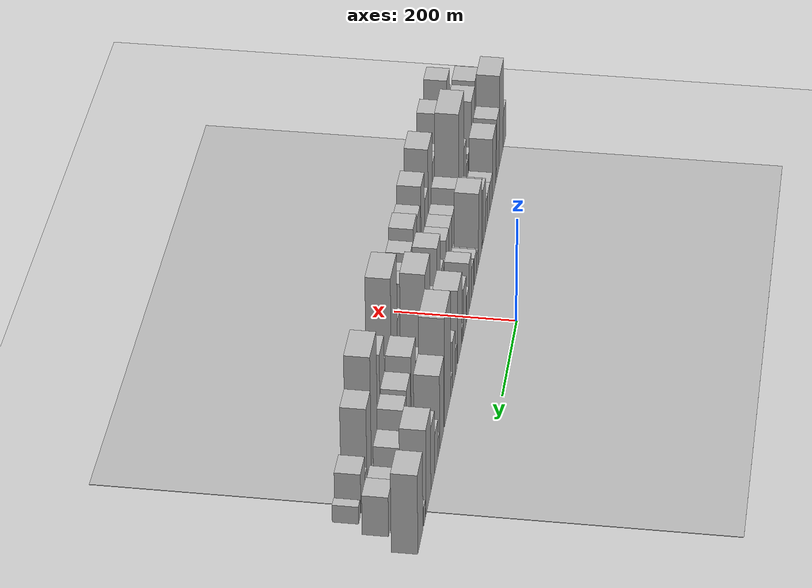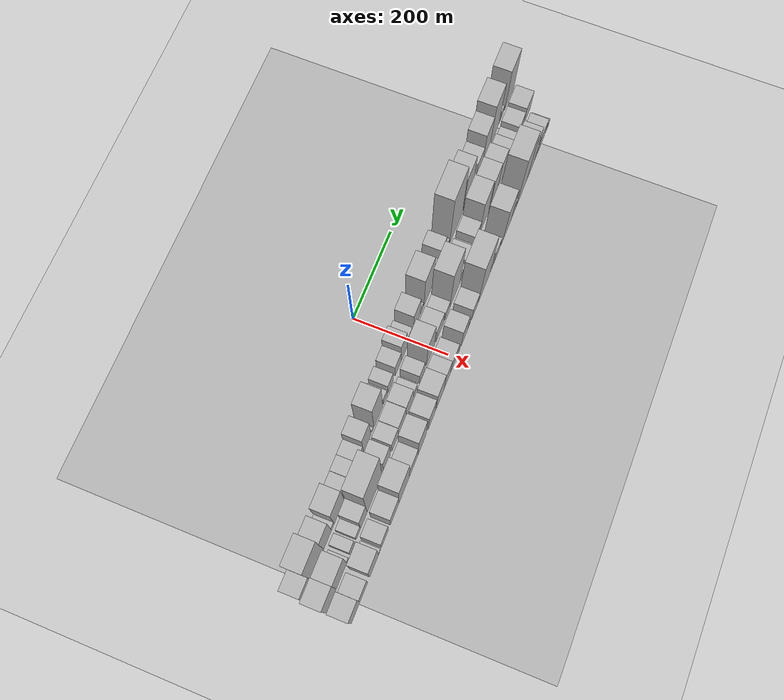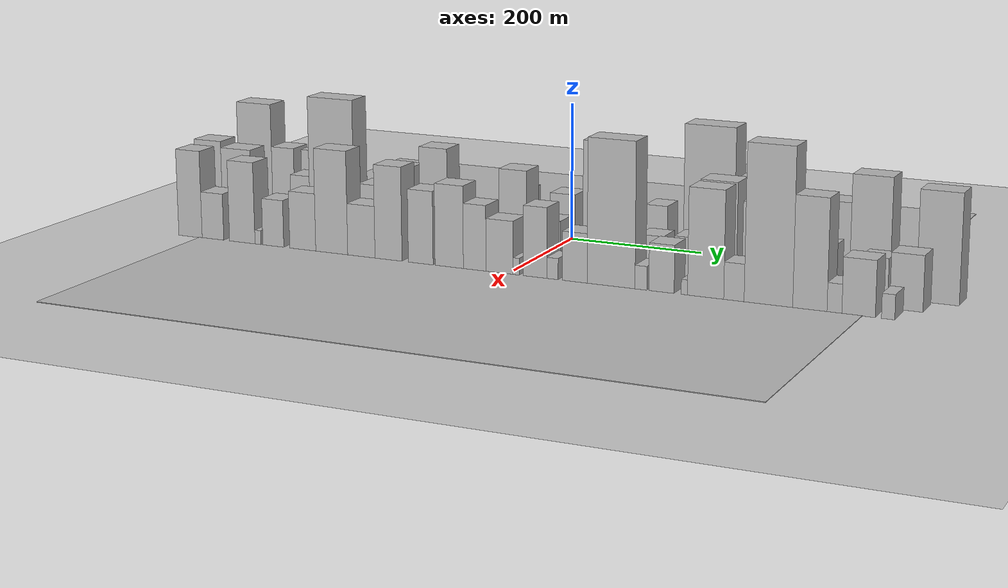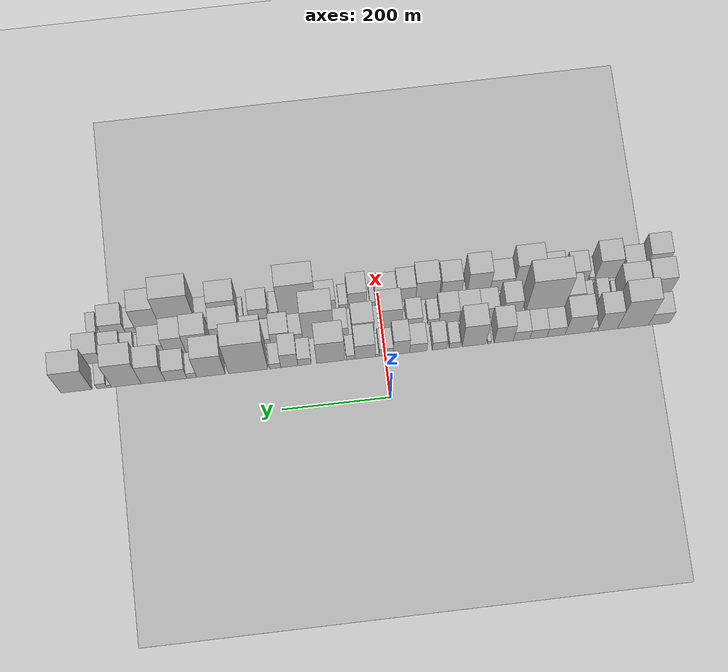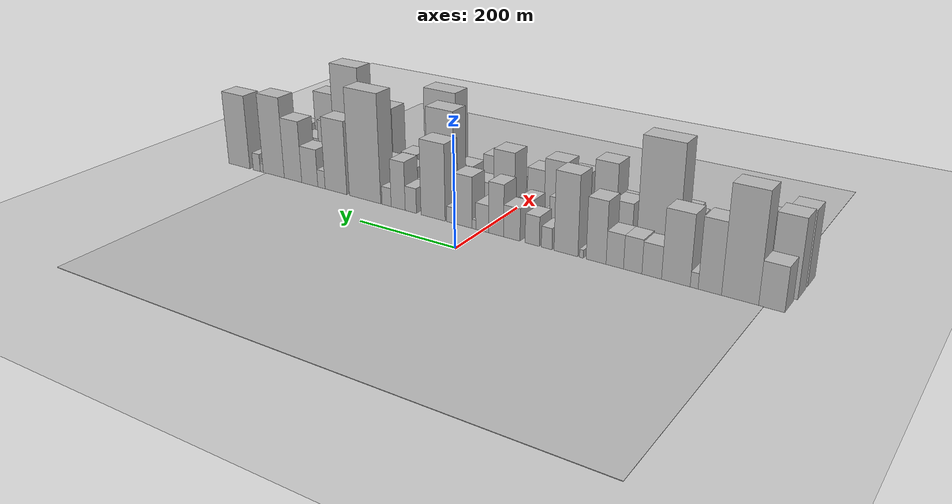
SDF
<?xml version="1.0" encoding="utf-8"?>

<sdf version="1.6">

   <world name="default">

      <gui fullscreen="0">

         <camera name="user_camera">

            <pose>-15 0 4.57585 0 0 0</pose>

            <view_controller>orbit</view_controller>

         </camera>

      </gui>

      <scene>

         <sky>

           <clouds>

             <speed>12</speed>

           </clouds>

         </sky>

         <ambient>0.4 0.4 0.4 1</ambient>

         <background>0.7 0.7 0.7 1</background>

         <shadows>1</shadows>

      </scene>

      <gravity>0 0 -9.8066</gravity>

      <magnetic_field>6e-06 2.3e-05 -4.2e-05</magnetic_field>

      <physics default="0" name="default_physics" type="ode">

         <ode>

            <solver>

               <type>quick</type>

               <iters>10</iters>

               <sor>1.0</sor>

               <use_dynamic_moi_rescaling>0</use_dynamic_moi_rescaling>

            </solver>

            <constraints>

               <cfm>0</cfm>

               <erp>0.2</erp>

               <contact_max_correcting_vel>100</contact_max_correcting_vel>

               <contact_surface_layer>0.001</contact_surface_layer>

            </constraints>

         </ode>

         <max_step_size>0.004</max_step_size>

         <real_time_factor>1</real_time_factor>

         <real_time_update_rate>250</real_time_update_rate>

      </physics>

      <light name="sun" type="directional">

         <cast_shadows>1</cast_shadows>

         <pose>0 0 10 0 0 0</pose>

         <diffuse>0.8 0.8 0.8 1</diffuse>

         <specular>0.2 0.2 0.2 1</specular>

         <attenuation>

            <range>1000</range>

            <constant>0.9</constant>

            <linear>0.01</linear>

            <quadratic>0.001</quadratic>

         </attenuation>

         <direction>-0.5 0.1 -0.9</direction>

      </light>

      <include>

         <name>ground_plane_1</name>

         <uri>model://HANNAS_ground_plane</uri>

         <pose>0 0 0  0 0 0</pose>

      </include>

      <include>

         <name>ground_plane_2</name>

         <uri>model://HANNAS_ground_plane</uri>

         <pose>100 0 0  0 0 0</pose>

      </include>

      <model name="building_1">

         <static>1</static>

         <pose frame="">100.0000 -512.0443 0 0.000000 0.000000 0.000000</pose>

         <link name="link">

            <pose frame="">0 0 37.50 0 0 0</pose>

            <collision name="collision">

               <geometry>

                  <box>

                     <size>40.0000 39.9115 75.0000</size>

                  </box>

               </geometry>

               <max_contacts>10</max_contacts>

               <surface>

                  <contact>

                     <ode/>

                  </contact>

                  <bounce/>

                  <friction>

                     <torsional>

                        <ode/>

                     </torsional>

                     <ode/>

                  </friction>

               </surface>

            </collision>

            <visual name="visual">

               <cast_shadows>0</cast_shadows>

               <geometry>

                  <box>

                     <size>40.0000 39.9115 75.0000</size>

                  </box>

               </geometry>

               <material>

                  <script>

                     <uri>model://HANNAS_wall/materials/scripts</uri>

                     <uri>model://HANNAS_wall/materials/textures</uri>

                     <name>vrc/HANNAS_wall</name>

                  </script>

               </material>

            </visual>

            <self_collide>0</self_collide>

            <enable_wind>0</enable_wind>

            <kinematic>0</kinematic>

         </link>

      </model>

      <model name="building_2">

         <static>1</static>

         <pose frame="">100.0000 -462.9646 0 0.000000 0.000000 0.000000</pose>

         <link name="link">

            <pose frame="">0 0 93.00 0 0 0</pose>

            <collision name="collision">

               <geometry>

                  <box>

                     <size>40.0000 58.2478 186.0000</size>

                  </box>

               </geometry>

               <max_contacts>10</max_contacts>

               <surface>

                  <contact>

                     <ode/>

                  </contact>

                  <bounce/>

                  <friction>

                     <torsional>

                        <ode/>

                     </torsional>

                     <ode/>

                  </friction>

               </surface>

            </collision>

            <visual name="visual">

               <cast_shadows>0</cast_shadows>

               <geometry>

                  <box>

                     <size>40.0000 58.2478 186.0000</size>

                  </box>

               </geometry>

               <material>

                  <script>

                     <uri>model://HANNAS_wall/materials/scripts</uri>

                     <uri>model://HANNAS_wall/materials/textures</uri>

                     <name>vrc/HANNAS_wall</name>

                  </script>

               </material>

            </visual>

            <self_collide>0</self_collide>

            <enable_wind>0</enable_wind>

            <kinematic>0</kinematic>

         </link>

      </model>

      <model name="building_3">

         <static>1</static>

         <pose frame="">100.0000 -414.9623 0 0.000000 0.000000 0.000000</pose>

         <link name="link">

            <pose frame="">0 0 61.50 0 0 0</pose>

            <collision name="collision">

               <geometry>

                  <box>

                     <size>40.0000 37.7568 123.0000</size>

                  </box>

               </geometry>

               <max_contacts>10</max_contacts>

               <surface>

                  <contact>

                     <ode/>

                  </contact>

                  <bounce/>

                  <friction>

                     <torsional>

                        <ode/>

                     </torsional>

                     <ode/>

                  </friction>

               </surface>

            </collision>

            <visual name="visual">

               <cast_shadows>0</cast_shadows>

               <geometry>

                  <box>

                     <size>40.0000 37.7568 123.0000</size>

                  </box>

               </geometry>

               <material>

                  <script>

                     <uri>model://HANNAS_wall/materials/scripts</uri>

                     <uri>model://HANNAS_wall/materials/textures</uri>

                     <name>vrc/HANNAS_wall</name>

                  </script>

               </material>

            </visual>

            <self_collide>0</self_collide>

            <enable_wind>0</enable_wind>

            <kinematic>0</kinematic>

         </link>

      </model>

      <model name="building_4">

         <static>1</static>

         <pose frame="">100.0000 -389.6329 0 0.000000 0.000000 0.000000</pose>

         <link name="link">

            <pose frame="">0 0 13.50 0 0 0</pose>

            <collision name="collision">

               <geometry>

                  <box>

                     <size>40.0000 12.9021 27.0000</size>

                  </box>

               </geometry>

               <max_contacts>10</max_contacts>

               <surface>

                  <contact>

                     <ode/>

                  </contact>

                  <bounce/>

                  <friction>

                     <torsional>

                        <ode/>

                     </torsional>

                     <ode/>

                  </friction>

               </surface>

            </collision>

            <visual name="visual">

               <cast_shadows>0</cast_shadows>

               <geometry>

                  <box>

                     <size>40.0000 12.9021 27.0000</size>

                  </box>

               </geometry>

               <material>

                  <script>

                     <uri>model://HANNAS_wall/materials/scripts</uri>

                     <uri>model://HANNAS_wall/materials/textures</uri>

                     <name>vrc/HANNAS_wall</name>

                  </script>

               </material>

            </visual>

            <self_collide>0</self_collide>

            <enable_wind>0</enable_wind>

            <kinematic>0</kinematic>

         </link>

      </model>

      <model name="building_5">

         <static>1</static>

         <pose frame="">100.0000 -359.2586 0 0.000000 0.000000 0.000000</pose>

         <link name="link">

            <pose frame="">0 0 61.50 0 0 0</pose>

            <collision name="collision">

               <geometry>

                  <box>

                     <size>40.0000 47.8465 123.0000</size>

                  </box>

               </geometry>

               <max_contacts>10</max_contacts>

               <surface>

                  <contact>

                     <ode/>

                  </contact>

                  <bounce/>

                  <friction>

                     <torsional>

                        <ode/>

                     </torsional>

                     <ode/>

                  </friction>

               </surface>

            </collision>

            <visual name="visual">

               <cast_shadows>0</cast_shadows>

               <geometry>

                  <box>

                     <size>40.0000 47.8465 123.0000</size>

                  </box>

               </geometry>

               <material>

                  <script>

                     <uri>model://HANNAS_wall/materials/scripts</uri>

                     <uri>model://HANNAS_wall/materials/textures</uri>

                     <name>vrc/HANNAS_wall</name>

                  </script>

               </material>

            </visual>

            <self_collide>0</self_collide>

            <enable_wind>0</enable_wind>

            <kinematic>0</kinematic>

         </link>

      </model>

      <model name="building_6">

         <static>1</static>

         <pose frame="">100.0000 -318.5789 0 0.000000 0.000000 0.000000</pose>

         <link name="link">

            <pose frame="">0 0 28.50 0 0 0</pose>

            <collision name="collision">

               <geometry>

                  <box>

                     <size>40.0000 33.5130 57.0000</size>

                  </box>

               </geometry>

               <max_contacts>10</max_contacts>

               <surface>

                  <contact>

                     <ode/>

                  </contact>

                  <bounce/>

                  <friction>

                     <torsional>

                        <ode/>

                     </torsional>

                     <ode/>

                  </friction>

               </surface>

            </collision>

            <visual name="visual">

               <cast_shadows>0</cast_shadows>

               <geometry>

                  <box>

                     <size>40.0000 33.5130 57.0000</size>

                  </box>

               </geometry>

               <material>

                  <script>

                     <uri>model://HANNAS_wall/materials/scripts</uri>

                     <uri>model://HANNAS_wall/materials/textures</uri>

                     <name>vrc/HANNAS_wall</name>

                  </script>

               </material>

            </visual>

            <self_collide>0</self_collide>

            <enable_wind>0</enable_wind>

            <kinematic>0</kinematic>

         </link>

      </model>

      <model name="building_7">

         <static>1</static>

         <pose frame="">100.0000 -285.7807 0 0.000000 0.000000 0.000000</pose>

         <link name="link">

            <pose frame="">0 0 30.00 0 0 0</pose>

            <collision name="collision">

               <geometry>

                  <box>

                     <size>40.0000 32.0833 60.0000</size>

                  </box>

               </geometry>

               <max_contacts>10</max_contacts>

               <surface>

                  <contact>

                     <ode/>

                  </contact>

                  <bounce/>

                  <friction>

                     <torsional>

                        <ode/>

                     </torsional>

                     <ode/>

                  </friction>

               </surface>

            </collision>

            <visual name="visual">

               <cast_shadows>0</cast_shadows>

               <geometry>

                  <box>

                     <size>40.0000 32.0833 60.0000</size>

                  </box>

               </geometry>

               <material>

                  <script>

                     <uri>model://HANNAS_wall/materials/scripts</uri>

                     <uri>model://HANNAS_wall/materials/textures</uri>

                     <name>vrc/HANNAS_wall</name>

                  </script>

               </material>

            </visual>

            <self_collide>0</self_collide>

            <enable_wind>0</enable_wind>

            <kinematic>0</kinematic>

         </link>

      </model>

      <model name="building_8">

         <static>1</static>

         <pose frame="">100.0000 -254.2660 0 0.000000 0.000000 0.000000</pose>

         <link name="link">

            <pose frame="">0 0 30.00 0 0 0</pose>

            <collision name="collision">

               <geometry>

                  <box>

                     <size>40.0000 30.9462 60.0000</size>

                  </box>

               </geometry>

               <max_contacts>10</max_contacts>

               <surface>

                  <contact>

                     <ode/>

                  </contact>

                  <bounce/>

                  <friction>

                     <torsional>

                        <ode/>

                     </torsional>

                     <ode/>

                  </friction>

               </surface>

            </collision>

            <visual name="visual">

               <cast_shadows>0</cast_shadows>

               <geometry>

                  <box>

                     <size>40.0000 30.9462 60.0000</size>

                  </box>

               </geometry>

               <material>

                  <script>

                     <uri>model://HANNAS_wall/materials/scripts</uri>

                     <uri>model://HANNAS_wall/materials/textures</uri>

                     <name>vrc/HANNAS_wall</name>

                  </script>

               </material>

            </visual>

            <self_collide>0</self_collide>

            <enable_wind>0</enable_wind>

            <kinematic>0</kinematic>

         </link>

      </model>

      <model name="building_9">

         <static>1</static>

         <pose frame="">100.0000 -220.7364 0 0.000000 0.000000 0.000000</pose>

         <link name="link">

            <pose frame="">0 0 55.50 0 0 0</pose>

            <collision name="collision">

               <geometry>

                  <box>

                     <size>40.0000 36.1131 111.0000</size>

                  </box>

               </geometry>

               <max_contacts>10</max_contacts>

               <surface>

                  <contact>

                     <ode/>

                  </contact>

                  <bounce/>

                  <friction>

                     <torsional>

                        <ode/>

                     </torsional>

                     <ode/>

                  </friction>

               </surface>

            </collision>

            <visual name="visual">

               <cast_shadows>0</cast_shadows>

               <geometry>

                  <box>

                     <size>40.0000 36.1131 111.0000</size>

                  </box>

               </geometry>

               <material>

                  <script>

                     <uri>model://HANNAS_wall/materials/scripts</uri>

                     <uri>model://HANNAS_wall/materials/textures</uri>

                     <name>vrc/HANNAS_wall</name>

                  </script>

               </material>

            </visual>

            <self_collide>0</self_collide>

            <enable_wind>0</enable_wind>

            <kinematic>0</kinematic>

         </link>

      </model>

      <model name="building_10">

         <static>1</static>

         <pose frame="">100.0000 -194.1090 0 0.000000 0.000000 0.000000</pose>

         <link name="link">

            <pose frame="">0 0 7.50 0 0 0</pose>

            <collision name="collision">

               <geometry>

                  <box>

                     <size>40.0000 7.1417 15.0000</size>

                  </box>

               </geometry>

               <max_contacts>10</max_contacts>

               <surface>

                  <contact>

                     <ode/>

                  </contact>

                  <bounce/>

                  <friction>

                     <torsional>

                        <ode/>

                     </torsional>

                     <ode/>

                  </friction>

               </surface>

            </collision>

            <visual name="visual">

               <cast_shadows>0</cast_shadows>

               <geometry>

                  <box>

                     <size>40.0000 7.1417 15.0000</size>

                  </box>

               </geometry>

               <material>

                  <script>

                     <uri>model://HANNAS_wall/materials/scripts</uri>

                     <uri>model://HANNAS_wall/materials/textures</uri>

                     <name>vrc/HANNAS_wall</name>

                  </script>

               </material>

            </visual>

            <self_collide>0</self_collide>

            <enable_wind>0</enable_wind>

            <kinematic>0</kinematic>

         </link>

      </model>

      <model name="building_11">

         <static>1</static>

         <pose frame="">100.0000 -165.2680 0 0.000000 0.000000 0.000000</pose>

         <link name="link">

            <pose frame="">0 0 72.00 0 0 0</pose>

            <collision name="collision">

               <geometry>

                  <box>

                     <size>40.0000 44.5402 144.0000</size>

                  </box>

               </geometry>

               <max_contacts>10</max_contacts>

               <surface>

                  <contact>

                     <ode/>

                  </contact>

                  <bounce/>

                  <friction>

                     <torsional>

                        <ode/>

                     </torsional>

                     <ode/>

                  </friction>

               </surface>

            </collision>

            <visual name="visual">

               <cast_shadows>0</cast_shadows>

               <geometry>

                  <box>

                     <size>40.0000 44.5402 144.0000</size>

                  </box>

               </geometry>

               <material>

                  <script>

                     <uri>model://HANNAS_wall/materials/scripts</uri>

                     <uri>model://HANNAS_wall/materials/textures</uri>

                     <name>vrc/HANNAS_wall</name>

                  </script>

               </material>

            </visual>

            <self_collide>0</self_collide>

            <enable_wind>0</enable_wind>

            <kinematic>0</kinematic>

         </link>

      </model>

      <model name="building_12">

         <static>1</static>

         <pose frame="">100.0000 -128.9240 0 0.000000 0.000000 0.000000</pose>

         <link name="link">

            <pose frame="">0 0 19.50 0 0 0</pose>

            <collision name="collision">

               <geometry>

                  <box>

                     <size>40.0000 20.1479 39.0000</size>

                  </box>

               </geometry>

               <max_contacts>10</max_contacts>

               <surface>

                  <contact>

                     <ode/>

                  </contact>

                  <bounce/>

                  <friction>

                     <torsional>

                        <ode/>

                     </torsional>

                     <ode/>

                  </friction>

               </surface>

            </collision>

            <visual name="visual">

               <cast_shadows>0</cast_shadows>

               <geometry>

                  <box>

                     <size>40.0000 20.1479 39.0000</size>

                  </box>

               </geometry>

               <material>

                  <script>

                     <uri>model://HANNAS_wall/materials/scripts</uri>

                     <uri>model://HANNAS_wall/materials/textures</uri>

                     <name>vrc/HANNAS_wall</name>

                  </script>

               </material>

            </visual>

            <self_collide>0</self_collide>

            <enable_wind>0</enable_wind>

            <kinematic>0</kinematic>

         </link>

      </model>

      <model name="building_13">

         <static>1</static>

         <pose frame="">100.0000 -101.1259 0 0.000000 0.000000 0.000000</pose>

         <link name="link">

            <pose frame="">0 0 27.00 0 0 0</pose>

            <collision name="collision">

               <geometry>

                  <box>

                     <size>40.0000 27.4483 54.0000</size>

                  </box>

               </geometry>

               <max_contacts>10</max_contacts>

               <surface>

                  <contact>

                     <ode/>

                  </contact>

                  <bounce/>

                  <friction>

                     <torsional>

                        <ode/>

                     </torsional>

                     <ode/>

                  </friction>

               </surface>

            </collision>

            <visual name="visual">

               <cast_shadows>0</cast_shadows>

               <geometry>

                  <box>

                     <size>40.0000 27.4483 54.0000</size>

                  </box>

               </geometry>

               <material>

                  <script>

                     <uri>model://HANNAS_wall/materials/scripts</uri>

                     <uri>model://HANNAS_wall/materials/textures</uri>

                     <name>vrc/HANNAS_wall</name>

                  </script>

               </material>

            </visual>

            <self_collide>0</self_collide>

            <enable_wind>0</enable_wind>

            <kinematic>0</kinematic>

         </link>

      </model>

      <model name="building_14">

         <static>1</static>

         <pose frame="">100.0000 -61.3096 0 0.000000 0.000000 0.000000</pose>

         <link name="link">

            <pose frame="">0 0 30.00 0 0 0</pose>

            <collision name="collision">

               <geometry>

                  <box>

                     <size>40.0000 32.1842 60.0000</size>

                  </box>

               </geometry>

               <max_contacts>10</max_contacts>

               <surface>

                  <contact>

                     <ode/>

                  </contact>

                  <bounce/>

                  <friction>

                     <torsional>

                        <ode/>

                     </torsional>

                     <ode/>

                  </friction>

               </surface>

            </collision>

            <visual name="visual">

               <cast_shadows>0</cast_shadows>

               <geometry>

                  <box>

                     <size>40.0000 32.1842 60.0000</size>

                  </box>

               </geometry>

               <material>

                  <script>

                     <uri>model://HANNAS_wall/materials/scripts</uri>

                     <uri>model://HANNAS_wall/materials/textures</uri>

                     <name>vrc/HANNAS_wall</name>

                  </script>

               </material>

            </visual>

            <self_collide>0</self_collide>

            <enable_wind>0</enable_wind>

            <kinematic>0</kinematic>

         </link>

      </model>

      <model name="building_15">

         <static>1</static>

         <pose frame="">100.0000 -29.9201 0 0.000000 0.000000 0.000000</pose>

         <link name="link">

            <pose frame="">0 0 48.00 0 0 0</pose>

            <collision name="collision">

               <geometry>

                  <box>

                     <size>40.0000 30.5947 96.0000</size>

                  </box>

               </geometry>

               <max_contacts>10</max_contacts>

               <surface>

                  <contact>

                     <ode/>

                  </contact>

                  <bounce/>

                  <friction>

                     <torsional>

                        <ode/>

                     </torsional>

                     <ode/>

                  </friction>

               </surface>

            </collision>

            <visual name="visual">

               <cast_shadows>0</cast_shadows>

               <geometry>

                  <box>

                     <size>40.0000 30.5947 96.0000</size>

                  </box>

               </geometry>

               <material>

                  <script>

                     <uri>model://HANNAS_wall/materials/scripts</uri>

                     <uri>model://HANNAS_wall/materials/textures</uri>

                     <name>vrc/HANNAS_wall</name>

                  </script>

               </material>

            </visual>

            <self_collide>0</self_collide>

            <enable_wind>0</enable_wind>

            <kinematic>0</kinematic>

         </link>

      </model>

      <model name="building_16">

         <static>1</static>

         <pose frame="">100.0000 -1.5461 0 0.000000 0.000000 0.000000</pose>

         <link name="link">

            <pose frame="">0 0 25.50 0 0 0</pose>

            <collision name="collision">

               <geometry>

                  <box>

                     <size>40.0000 26.1533 51.0000</size>

                  </box>

               </geometry>

               <max_contacts>10</max_contacts>

               <surface>

                  <contact>

                     <ode/>

                  </contact>

                  <bounce/>

                  <friction>

                     <torsional>

                        <ode/>

                     </torsional>

                     <ode/>

                  </friction>

               </surface>

            </collision>

            <visual name="visual">

               <cast_shadows>0</cast_shadows>

               <geometry>

                  <box>

                     <size>40.0000 26.1533 51.0000</size>

                  </box>

               </geometry>

               <material>

                  <script>

                     <uri>model://HANNAS_wall/materials/scripts</uri>

                     <uri>model://HANNAS_wall/materials/textures</uri>

                     <name>vrc/HANNAS_wall</name>

                  </script>

               </material>

            </visual>

            <self_collide>0</self_collide>

            <enable_wind>0</enable_wind>

            <kinematic>0</kinematic>

         </link>

      </model>

      <model name="building_17">

         <static>1</static>

         <pose frame="">100.0000 15.2226 0 0.000000 0.000000 0.000000</pose>

         <link name="link">

            <pose frame="">0 0 9.00 0 0 0</pose>

            <collision name="collision">

               <geometry>

                  <box>

                     <size>40.0000 7.3841 18.0000</size>

                  </box>

               </geometry>

               <max_contacts>10</max_contacts>

               <surface>

                  <contact>

                     <ode/>

                  </contact>

                  <bounce/>

                  <friction>

                     <torsional>

                        <ode/>

                     </torsional>

                     <ode/>

                  </friction>

               </surface>

            </collision>

            <visual name="visual">

               <cast_shadows>0</cast_shadows>

               <geometry>

                  <box>

                     <size>40.0000 7.3841 18.0000</size>

                  </box>

               </geometry>

               <material>

                  <script>

                     <uri>model://HANNAS_wall/materials/scripts</uri>

                     <uri>model://HANNAS_wall/materials/textures</uri>

                     <name>vrc/HANNAS_wall</name>

                  </script>

               </material>

            </visual>

            <self_collide>0</self_collide>

            <enable_wind>0</enable_wind>

            <kinematic>0</kinematic>

         </link>

      </model>

      <model name="building_18">

         <static>1</static>

         <pose frame="">100.0000 37.8228 0 0.000000 0.000000 0.000000</pose>

         <link name="link">

            <pose frame="">0 0 48.00 0 0 0</pose>

            <collision name="collision">

               <geometry>

                  <box>

                     <size>40.0000 37.8164 96.0000</size>

                  </box>

               </geometry>

               <max_contacts>10</max_contacts>

               <surface>

                  <contact>

                     <ode/>

                  </contact>

                  <bounce/>

                  <friction>

                     <torsional>

                        <ode/>

                     </torsional>

                     <ode/>

                  </friction>

               </surface>

            </collision>

            <visual name="visual">

               <cast_shadows>0</cast_shadows>

               <geometry>

                  <box>

                     <size>40.0000 37.8164 96.0000</size>

                  </box>

               </geometry>

               <material>

                  <script>

                     <uri>model://HANNAS_wall/materials/scripts</uri>

                     <uri>model://HANNAS_wall/materials/textures</uri>

                     <name>vrc/HANNAS_wall</name>

                  </script>

               </material>

            </visual>

            <self_collide>0</self_collide>

            <enable_wind>0</enable_wind>

            <kinematic>0</kinematic>

         </link>

      </model>

      <model name="building_19">

         <static>1</static>

         <pose frame="">100.0000 64.6895 0 0.000000 0.000000 0.000000</pose>

         <link name="link">

            <pose frame="">0 0 15.00 0 0 0</pose>

            <collision name="collision">

               <geometry>

                  <box>

                     <size>40.0000 15.9169 30.0000</size>

                  </box>

               </geometry>

               <max_contacts>10</max_contacts>

               <surface>

                  <contact>

                     <ode/>

                  </contact>

                  <bounce/>

                  <friction>

                     <torsional>

                        <ode/>

                     </torsional>

                     <ode/>

                  </friction>

               </surface>

            </collision>

            <visual name="visual">

               <cast_shadows>0</cast_shadows>

               <geometry>

                  <box>

                     <size>40.0000 15.9169 30.0000</size>

                  </box>

               </geometry>

               <material>

                  <script>

                     <uri>model://HANNAS_wall/materials/scripts</uri>

                     <uri>model://HANNAS_wall/materials/textures</uri>

                     <name>vrc/HANNAS_wall</name>

                  </script>

               </material>

            </visual>

            <self_collide>0</self_collide>

            <enable_wind>0</enable_wind>

            <kinematic>0</kinematic>

         </link>

      </model>

      <model name="building_20">

         <static>1</static>

         <pose frame="">100.0000 101.7479 0 0.000000 0.000000 0.000000</pose>

         <link name="link">

            <pose frame="">0 0 72.00 0 0 0</pose>

            <collision name="collision">

               <geometry>

                  <box>

                     <size>40.0000 52.1997 144.0000</size>

                  </box>

               </geometry>

               <max_contacts>10</max_contacts>

               <surface>

                  <contact>

                     <ode/>

                  </contact>

                  <bounce/>

                  <friction>

                     <torsional>

                        <ode/>

                     </torsional>

                     <ode/>

                  </friction>

               </surface>

            </collision>

            <visual name="visual">

               <cast_shadows>0</cast_shadows>

               <geometry>

                  <box>

                     <size>40.0000 52.1997 144.0000</size>

                  </box>

               </geometry>

               <material>

                  <script>

                     <uri>model://HANNAS_wall/materials/scripts</uri>

                     <uri>model://HANNAS_wall/materials/textures</uri>

                     <name>vrc/HANNAS_wall</name>

                  </script>

               </material>

            </visual>

            <self_collide>0</self_collide>

            <enable_wind>0</enable_wind>

            <kinematic>0</kinematic>

         </link>

      </model>

      <model name="building_21">

         <static>1</static>

         <pose frame="">100.0000 150.2726 0 0.000000 0.000000 0.000000</pose>

         <link name="link">

            <pose frame="">0 0 24.00 0 0 0</pose>

            <collision name="collision">

               <geometry>

                  <box>

                     <size>40.0000 24.8498 48.0000</size>

                  </box>

               </geometry>

               <max_contacts>10</max_contacts>

               <surface>

                  <contact>

                     <ode/>

                  </contact>

                  <bounce/>

                  <friction>

                     <torsional>

                        <ode/>

                     </torsional>

                     <ode/>

                  </friction>

               </surface>

            </collision>

            <visual name="visual">

               <cast_shadows>0</cast_shadows>

               <geometry>

                  <box>

                     <size>40.0000 24.8498 48.0000</size>

                  </box>

               </geometry>

               <material>

                  <script>

                     <uri>model://HANNAS_wall/materials/scripts</uri>

                     <uri>model://HANNAS_wall/materials/textures</uri>

                     <name>vrc/HANNAS_wall</name>

                  </script>

               </material>

            </visual>

            <self_collide>0</self_collide>

            <enable_wind>0</enable_wind>

            <kinematic>0</kinematic>

         </link>

      </model>

      <model name="building_22">

         <static>1</static>

         <pose frame="">100.0000 178.5431 0 0.000000 0.000000 0.000000</pose>

         <link name="link">

            <pose frame="">0 0 46.50 0 0 0</pose>

            <collision name="collision">

               <geometry>

                  <box>

                     <size>40.0000 31.6912 93.0000</size>

                  </box>

               </geometry>

               <max_contacts>10</max_contacts>

               <surface>

                  <contact>

                     <ode/>

                  </contact>

                  <bounce/>

                  <friction>

                     <torsional>

                        <ode/>

                     </torsional>

                     <ode/>

                  </friction>

               </surface>

            </collision>

            <visual name="visual">

               <cast_shadows>0</cast_shadows>

               <geometry>

                  <box>

                     <size>40.0000 31.6912 93.0000</size>

                  </box>

               </geometry>

               <material>

                  <script>

                     <uri>model://HANNAS_wall/materials/scripts</uri>

                     <uri>model://HANNAS_wall/materials/textures</uri>

                     <name>vrc/HANNAS_wall</name>

                  </script>

               </material>

            </visual>

            <self_collide>0</self_collide>

            <enable_wind>0</enable_wind>

            <kinematic>0</kinematic>

         </link>

      </model>

      <model name="building_23">

         <static>1</static>

         <pose frame="">100.0000 204.7480 0 0.000000 0.000000 0.000000</pose>

         <link name="link">

            <pose frame="">0 0 18.00 0 0 0</pose>

            <collision name="collision">

               <geometry>

                  <box>

                     <size>40.0000 20.7185 36.0000</size>

                  </box>

               </geometry>

               <max_contacts>10</max_contacts>

               <surface>

                  <contact>

                     <ode/>

                  </contact>

                  <bounce/>

                  <friction>

                     <torsional>

                        <ode/>

                     </torsional>

                     <ode/>

                  </friction>

               </surface>

            </collision>

            <visual name="visual">

               <cast_shadows>0</cast_shadows>

               <geometry>

                  <box>

                     <size>40.0000 20.7185 36.0000</size>

                  </box>

               </geometry>

               <material>

                  <script>

                     <uri>model://HANNAS_wall/materials/scripts</uri>

                     <uri>model://HANNAS_wall/materials/textures</uri>

                     <name>vrc/HANNAS_wall</name>

                  </script>

               </material>

            </visual>

            <self_collide>0</self_collide>

            <enable_wind>0</enable_wind>

            <kinematic>0</kinematic>

         </link>

      </model>

      <model name="building_24">

         <static>1</static>

         <pose frame="">100.0000 254.8425 0 0.000000 0.000000 0.000000</pose>

         <link name="link">

            <pose frame="">0 0 105.00 0 0 0</pose>

            <collision name="collision">

               <geometry>

                  <box>

                     <size>40.0000 73.4706 210.0000</size>

                  </box>

               </geometry>

               <max_contacts>10</max_contacts>

               <surface>

                  <contact>

                     <ode/>

                  </contact>

                  <bounce/>

                  <friction>

                     <torsional>

                        <ode/>

                     </torsional>

                     <ode/>

                  </friction>

               </surface>

            </collision>

            <visual name="visual">

               <cast_shadows>0</cast_shadows>

               <geometry>

                  <box>

                     <size>40.0000 73.4706 210.0000</size>

                  </box>

               </geometry>

               <material>

                  <script>

                     <uri>model://HANNAS_wall/materials/scripts</uri>

                     <uri>model://HANNAS_wall/materials/textures</uri>

                     <name>vrc/HANNAS_wall</name>

                  </script>

               </material>

            </visual>

            <self_collide>0</self_collide>

            <enable_wind>0</enable_wind>

            <kinematic>0</kinematic>

         </link>

      </model>

      <model name="building_25">

         <static>1</static>

         <pose frame="">100.0000 323.9424 0 0.000000 0.000000 0.000000</pose>

         <link name="link">

            <pose frame="">0 0 72.00 0 0 0</pose>

            <collision name="collision">

               <geometry>

                  <box>

                     <size>40.0000 52.7291 144.0000</size>

                  </box>

               </geometry>

               <max_contacts>10</max_contacts>

               <surface>

                  <contact>

                     <ode/>

                  </contact>

                  <bounce/>

                  <friction>

                     <torsional>

                        <ode/>

                     </torsional>

                     <ode/>

                  </friction>

               </surface>

            </collision>

            <visual name="visual">

               <cast_shadows>0</cast_shadows>

               <geometry>

                  <box>

                     <size>40.0000 52.7291 144.0000</size>

                  </box>

               </geometry>

               <material>

                  <script>

                     <uri>model://HANNAS_wall/materials/scripts</uri>

                     <uri>model://HANNAS_wall/materials/textures</uri>

                     <name>vrc/HANNAS_wall</name>

                  </script>

               </material>

            </visual>

            <self_collide>0</self_collide>

            <enable_wind>0</enable_wind>

            <kinematic>0</kinematic>

         </link>

      </model>

      <model name="building_26">

         <static>1</static>

         <pose frame="">100.0000 359.3144 0 0.000000 0.000000 0.000000</pose>

         <link name="link">

            <pose frame="">0 0 18.00 0 0 0</pose>

            <collision name="collision">

               <geometry>

                  <box>

                     <size>40.0000 18.0149 36.0000</size>

                  </box>

               </geometry>

               <max_contacts>10</max_contacts>

               <surface>

                  <contact>

                     <ode/>

                  </contact>

                  <bounce/>

                  <friction>

                     <torsional>

                        <ode/>

                     </torsional>

                     <ode/>

                  </friction>

               </surface>

            </collision>

            <visual name="visual">

               <cast_shadows>0</cast_shadows>

               <geometry>

                  <box>

                     <size>40.0000 18.0149 36.0000</size>

                  </box>

               </geometry>

               <material>

                  <script>

                     <uri>model://HANNAS_wall/materials/scripts</uri>

                     <uri>model://HANNAS_wall/materials/textures</uri>

                     <name>vrc/HANNAS_wall</name>

                  </script>

               </material>

            </visual>

            <self_collide>0</self_collide>

            <enable_wind>0</enable_wind>

            <kinematic>0</kinematic>

         </link>

      </model>

      <model name="building_27">

         <static>1</static>

         <pose frame="">100.0000 388.4351 0 0.000000 0.000000 0.000000</pose>

         <link name="link">

            <pose frame="">0 0 37.50 0 0 0</pose>

            <collision name="collision">

               <geometry>

                  <box>

                     <size>40.0000 40.2265 75.0000</size>

                  </box>

               </geometry>

               <max_contacts>10</max_contacts>

               <surface>

                  <contact>

                     <ode/>

                  </contact>

                  <bounce/>

                  <friction>

                     <torsional>

                        <ode/>

                     </torsional>

                     <ode/>

                  </friction>

               </surface>

            </collision>

            <visual name="visual">

               <cast_shadows>0</cast_shadows>

               <geometry>

                  <box>

                     <size>40.0000 40.2265 75.0000</size>

                  </box>

               </geometry>

               <material>

                  <script>

                     <uri>model://HANNAS_wall/materials/scripts</uri>

                     <uri>model://HANNAS_wall/materials/textures</uri>

                     <name>vrc/HANNAS_wall</name>

                  </script>

               </material>

            </visual>

            <self_collide>0</self_collide>

            <enable_wind>0</enable_wind>

            <kinematic>0</kinematic>

         </link>

      </model>

      <model name="building_28">

         <static>1</static>

         <pose frame="">100.0000 430.8241 0 0.000000 0.000000 0.000000</pose>

         <link name="link">

            <pose frame="">0 0 61.50 0 0 0</pose>

            <collision name="collision">

               <geometry>

                  <box>

                     <size>40.0000 44.5515 123.0000</size>

                  </box>

               </geometry>

               <max_contacts>10</max_contacts>

               <surface>

                  <contact>

                     <ode/>

                  </contact>

                  <bounce/>

                  <friction>

                     <torsional>

                        <ode/>

                     </torsional>

                     <ode/>

                  </friction>

               </surface>

            </collision>

            <visual name="visual">

               <cast_shadows>0</cast_shadows>

               <geometry>

                  <box>

                     <size>40.0000 44.5515 123.0000</size>

                  </box>

               </geometry>

               <material>

                  <script>

                     <uri>model://HANNAS_wall/materials/scripts</uri>

                     <uri>model://HANNAS_wall/materials/textures</uri>

                     <name>vrc/HANNAS_wall</name>

                  </script>

               </material>

            </visual>

            <self_collide>0</self_collide>

            <enable_wind>0</enable_wind>

            <kinematic>0</kinematic>

         </link>

      </model>

      <model name="building_29">

         <static>1</static>

         <pose frame="">100.0000 480.5783 0 0.000000 0.000000 0.000000</pose>

         <link name="link">

            <pose frame="">0 0 81.00 0 0 0</pose>

            <collision name="collision">

               <geometry>

                  <box>

                     <size>40.0000 54.9570 162.0000</size>

                  </box>

               </geometry>

               <max_contacts>10</max_contacts>

               <surface>

                  <contact>

                     <ode/>

                  </contact>

                  <bounce/>

                  <friction>

                     <torsional>

                        <ode/>

                     </torsional>

                     <ode/>

                  </friction>

               </surface>

            </collision>

            <visual name="visual">

               <cast_shadows>0</cast_shadows>

               <geometry>

                  <box>

                     <size>40.0000 54.9570 162.0000</size>

                  </box>

               </geometry>

               <material>

                  <script>

                     <uri>model://HANNAS_wall/materials/scripts</uri>

                     <uri>model://HANNAS_wall/materials/textures</uri>

                     <name>vrc/HANNAS_wall</name>

                  </script>

               </material>

            </visual>

            <self_collide>0</self_collide>

            <enable_wind>0</enable_wind>

            <kinematic>0</kinematic>

         </link>

      </model>

      <model name="building_30">

         <static>1</static>

         <pose frame="">100.0000 512.0214 0 0.000000 0.000000 0.000000</pose>

         <link name="link">

            <pose frame="">0 0 9.00 0 0 0</pose>

            <collision name="collision">

               <geometry>

                  <box>

                     <size>40.0000 7.9293 18.0000</size>

                  </box>

               </geometry>

               <max_contacts>10</max_contacts>

               <surface>

                  <contact>

                     <ode/>

                  </contact>

                  <bounce/>

                  <friction>

                     <torsional>

                        <ode/>

                     </torsional>

                     <ode/>

                  </friction>

               </surface>

            </collision>

            <visual name="visual">

               <cast_shadows>0</cast_shadows>

               <geometry>

                  <box>

                     <size>40.0000 7.9293 18.0000</size>

                  </box>

               </geometry>

               <material>

                  <script>

                     <uri>model://HANNAS_wall/materials/scripts</uri>

                     <uri>model://HANNAS_wall/materials/textures</uri>

                     <name>vrc/HANNAS_wall</name>

                  </script>

               </material>

            </visual>

            <self_collide>0</self_collide>

            <enable_wind>0</enable_wind>

            <kinematic>0</kinematic>

         </link>

      </model>

      <model name="building_31">

         <static>1</static>

         <pose frame="">100.0000 525.4122 0 0.000000 0.000000 0.000000</pose>

         <link name="link">

            <pose frame="">0 0 18.00 0 0 0</pose>

            <collision name="collision">

               <geometry>

                  <box>

                     <size>40.0000 18.8523 36.0000</size>

                  </box>

               </geometry>

               <max_contacts>10</max_contacts>

               <surface>

                  <contact>

                     <ode/>

                  </contact>

                  <bounce/>

                  <friction>

                     <torsional>

                        <ode/>

                     </torsional>

                     <ode/>

                  </friction>

               </surface>

            </collision>

            <visual name="visual">

               <cast_shadows>0</cast_shadows>

               <geometry>

                  <box>

                     <size>40.0000 18.8523 36.0000</size>

                  </box>

               </geometry>

               <material>

                  <script>

                     <uri>model://HANNAS_wall/materials/scripts</uri>

                     <uri>model://HANNAS_wall/materials/textures</uri>

                     <name>vrc/HANNAS_wall</name>

                  </script>

               </material>

            </visual>

            <self_collide>0</self_collide>

            <enable_wind>0</enable_wind>

            <kinematic>0</kinematic>

         </link>

      </model>

      <model name="building_32">

         <static>1</static>

         <pose frame="">100.0000 572.3750 0 0.000000 0.000000 0.000000</pose>

         <link name="link">

            <pose frame="">0 0 75.00 0 0 0</pose>

            <collision name="collision">

               <geometry>

                  <box>

                     <size>40.0000 57.0732 150.0000</size>

                  </box>

               </geometry>

               <max_contacts>10</max_contacts>

               <surface>

                  <contact>

                     <ode/>

                  </contact>

                  <bounce/>

                  <friction>

                     <torsional>

                        <ode/>

                     </torsional>

                     <ode/>

                  </friction>

               </surface>

            </collision>

            <visual name="visual">

               <cast_shadows>0</cast_shadows>

               <geometry>

                  <box>

                     <size>40.0000 57.0732 150.0000</size>

                  </box>

               </geometry>

               <material>

                  <script>

                     <uri>model://HANNAS_wall/materials/scripts</uri>

                     <uri>model://HANNAS_wall/materials/textures</uri>

                     <name>vrc/HANNAS_wall</name>

                  </script>

               </material>

            </visual>

            <self_collide>0</self_collide>

            <enable_wind>0</enable_wind>

            <kinematic>0</kinematic>

         </link>

      </model>

      <model name="building_33">

         <static>1</static>

         <pose frame="">149.0000 -513.2395 0 0.000000 0.000000 0.000000</pose>

         <link name="link">

            <pose frame="">0 0 67.50 0 0 0</pose>

            <collision name="collision">

               <geometry>

                  <box>

                     <size>40.0000 45.5210 135.0000</size>

                  </box>

               </geometry>

               <max_contacts>10</max_contacts>

               <surface>

                  <contact>

                     <ode/>

                  </contact>

                  <bounce/>

                  <friction>

                     <torsional>

                        <ode/>

                     </torsional>

                     <ode/>

                  </friction>

               </surface>

            </collision>

            <visual name="visual">

               <cast_shadows>0</cast_shadows>

               <geometry>

                  <box>

                     <size>40.0000 45.5210 135.0000</size>

                  </box>

               </geometry>

               <material>

                  <script>

                     <uri>model://HANNAS_wall/materials/scripts</uri>

                     <uri>model://HANNAS_wall/materials/textures</uri>

                     <name>vrc/HANNAS_wall</name>

                  </script>

               </material>

            </visual>

            <self_collide>0</self_collide>

            <enable_wind>0</enable_wind>

            <kinematic>0</kinematic>

         </link>

      </model>

      <model name="building_34">

         <static>1</static>

         <pose frame="">149.0000 -465.4376 0 0.000000 0.000000 0.000000</pose>

         <link name="link">

            <pose frame="">0 0 63.00 0 0 0</pose>

            <collision name="collision">

               <geometry>

                  <box>

                     <size>40.0000 50.0829 126.0000</size>

                  </box>

               </geometry>

               <max_contacts>10</max_contacts>

               <surface>

                  <contact>

                     <ode/>

                  </contact>

                  <bounce/>

                  <friction>

                     <torsional>

                        <ode/>

                     </torsional>

                     <ode/>

                  </friction>

               </surface>

            </collision>

            <visual name="visual">

               <cast_shadows>0</cast_shadows>

               <geometry>

                  <box>

                     <size>40.0000 50.0829 126.0000</size>

                  </box>

               </geometry>

               <material>

                  <script>

                     <uri>model://HANNAS_wall/materials/scripts</uri>

                     <uri>model://HANNAS_wall/materials/textures</uri>

                     <name>vrc/HANNAS_wall</name>

                  </script>

               </material>

            </visual>

            <self_collide>0</self_collide>

            <enable_wind>0</enable_wind>

            <kinematic>0</kinematic>

         </link>

      </model>

      <model name="building_35">

         <static>1</static>

         <pose frame="">149.0000 -436.0223 0 0.000000 0.000000 0.000000</pose>

         <link name="link">

            <pose frame="">0 0 9.00 0 0 0</pose>

            <collision name="collision">

               <geometry>

                  <box>

                     <size>40.0000 8.7476 18.0000</size>

                  </box>

               </geometry>

               <max_contacts>10</max_contacts>

               <surface>

                  <contact>

                     <ode/>

                  </contact>

                  <bounce/>

                  <friction>

                     <torsional>

                        <ode/>

                     </torsional>

                     <ode/>

                  </friction>

               </surface>

            </collision>

            <visual name="visual">

               <cast_shadows>0</cast_shadows>

               <geometry>

                  <box>

                     <size>40.0000 8.7476 18.0000</size>

                  </box>

               </geometry>

               <material>

                  <script>

                     <uri>model://HANNAS_wall/materials/scripts</uri>

                     <uri>model://HANNAS_wall/materials/textures</uri>

                     <name>vrc/HANNAS_wall</name>

                  </script>

               </material>

            </visual>

            <self_collide>0</self_collide>

            <enable_wind>0</enable_wind>

            <kinematic>0</kinematic>

         </link>

      </model>

      <model name="building_36">

         <static>1</static>

         <pose frame="">149.0000 -413.1563 0 0.000000 0.000000 0.000000</pose>

         <link name="link">

            <pose frame="">0 0 22.50 0 0 0</pose>

            <collision name="collision">

               <geometry>

                  <box>

                     <size>40.0000 22.9843 45.0000</size>

                  </box>

               </geometry>

               <max_contacts>10</max_contacts>

               <surface>

                  <contact>

                     <ode/>

                  </contact>

                  <bounce/>

                  <friction>

                     <torsional>

                        <ode/>

                     </torsional>

                     <ode/>

                  </friction>

               </surface>

            </collision>

            <visual name="visual">

               <cast_shadows>0</cast_shadows>

               <geometry>

                  <box>

                     <size>40.0000 22.9843 45.0000</size>

                  </box>

               </geometry>

               <material>

                  <script>

                     <uri>model://HANNAS_wall/materials/scripts</uri>

                     <uri>model://HANNAS_wall/materials/textures</uri>

                     <name>vrc/HANNAS_wall</name>

                  </script>

               </material>

            </visual>

            <self_collide>0</self_collide>

            <enable_wind>0</enable_wind>

            <kinematic>0</kinematic>

         </link>

      </model>

      <model name="building_37">

         <static>1</static>

         <pose frame="">149.0000 -384.3361 0 0.000000 0.000000 0.000000</pose>

         <link name="link">

            <pose frame="">0 0 19.50 0 0 0</pose>

            <collision name="collision">

               <geometry>

                  <box>

                     <size>40.0000 22.6561 39.0000</size>

                  </box>

               </geometry>

               <max_contacts>10</max_contacts>

               <surface>

                  <contact>

                     <ode/>

                  </contact>

                  <bounce/>

                  <friction>

                     <torsional>

                        <ode/>

                     </torsional>

                     <ode/>

                  </friction>

               </surface>

            </collision>

            <visual name="visual">

               <cast_shadows>0</cast_shadows>

               <geometry>

                  <box>

                     <size>40.0000 22.6561 39.0000</size>

                  </box>

               </geometry>

               <material>

                  <script>

                     <uri>model://HANNAS_wall/materials/scripts</uri>

                     <uri>model://HANNAS_wall/materials/textures</uri>

                     <name>vrc/HANNAS_wall</name>

                  </script>

               </material>

            </visual>

            <self_collide>0</self_collide>

            <enable_wind>0</enable_wind>

            <kinematic>0</kinematic>

         </link>

      </model>

      <model name="building_38">

         <static>1</static>

         <pose frame="">149.0000 -357.0428 0 0.000000 0.000000 0.000000</pose>

         <link name="link">

            <pose frame="">0 0 48.00 0 0 0</pose>

            <collision name="collision">

               <geometry>

                  <box>

                     <size>40.0000 31.9304 96.0000</size>

                  </box>

               </geometry>

               <max_contacts>10</max_contacts>

               <surface>

                  <contact>

                     <ode/>

                  </contact>

                  <bounce/>

                  <friction>

                     <torsional>

                        <ode/>

                     </torsional>

                     <ode/>

                  </friction>

               </surface>

            </collision>

            <visual name="visual">

               <cast_shadows>0</cast_shadows>

               <geometry>

                  <box>

                     <size>40.0000 31.9304 96.0000</size>

                  </box>

               </geometry>

               <material>

                  <script>

                     <uri>model://HANNAS_wall/materials/scripts</uri>

                     <uri>model://HANNAS_wall/materials/textures</uri>

                     <name>vrc/HANNAS_wall</name>

                  </script>

               </material>

            </visual>

            <self_collide>0</self_collide>

            <enable_wind>0</enable_wind>

            <kinematic>0</kinematic>

         </link>

      </model>

      <model name="building_39">

         <static>1</static>

         <pose frame="">149.0000 -304.5388 0 0.000000 0.000000 0.000000</pose>

         <link name="link">

            <pose frame="">0 0 106.50 0 0 0</pose>

            <collision name="collision">

               <geometry>

                  <box>

                     <size>40.0000 73.0776 213.0000</size>

                  </box>

               </geometry>

               <max_contacts>10</max_contacts>

               <surface>

                  <contact>

                     <ode/>

                  </contact>

                  <bounce/>

                  <friction>

                     <torsional>

                        <ode/>

                     </torsional>

                     <ode/>

                  </friction>

               </surface>

            </collision>

            <visual name="visual">

               <cast_shadows>0</cast_shadows>

               <geometry>

                  <box>

                     <size>40.0000 73.0776 213.0000</size>

                  </box>

               </geometry>

               <material>

                  <script>

                     <uri>model://HANNAS_wall/materials/scripts</uri>

                     <uri>model://HANNAS_wall/materials/textures</uri>

                     <name>vrc/HANNAS_wall</name>

                  </script>

               </material>

            </visual>

            <self_collide>0</self_collide>

            <enable_wind>0</enable_wind>

            <kinematic>0</kinematic>

         </link>

      </model>

      <model name="building_40">

         <static>1</static>

         <pose frame="">149.0000 -242.8486 0 0.000000 0.000000 0.000000</pose>

         <link name="link">

            <pose frame="">0 0 46.50 0 0 0</pose>

            <collision name="collision">

               <geometry>

                  <box>

                     <size>40.0000 34.3028 93.0000</size>

                  </box>

               </geometry>

               <max_contacts>10</max_contacts>

               <surface>

                  <contact>

                     <ode/>

                  </contact>

                  <bounce/>

                  <friction>

                     <torsional>

                        <ode/>

                     </torsional>

                     <ode/>

                  </friction>

               </surface>

            </collision>

            <visual name="visual">

               <cast_shadows>0</cast_shadows>

               <geometry>

                  <box>

                     <size>40.0000 34.3028 93.0000</size>

                  </box>

               </geometry>

               <material>

                  <script>

                     <uri>model://HANNAS_wall/materials/scripts</uri>

                     <uri>model://HANNAS_wall/materials/textures</uri>

                     <name>vrc/HANNAS_wall</name>

                  </script>

               </material>

            </visual>

            <self_collide>0</self_collide>

            <enable_wind>0</enable_wind>

            <kinematic>0</kinematic>

         </link>

      </model>

      <model name="building_41">

         <static>1</static>

         <pose frame="">149.0000 -200.7649 0 0.000000 0.000000 0.000000</pose>

         <link name="link">

            <pose frame="">0 0 33.00 0 0 0</pose>

            <collision name="collision">

               <geometry>

                  <box>

                     <size>40.0000 33.8648 66.0000</size>

                  </box>

               </geometry>

               <max_contacts>10</max_contacts>

               <surface>

                  <contact>

                     <ode/>

                  </contact>

                  <bounce/>

                  <friction>

                     <torsional>

                        <ode/>

                     </torsional>

                     <ode/>

                  </friction>

               </surface>

            </collision>

            <visual name="visual">

               <cast_shadows>0</cast_shadows>

               <geometry>

                  <box>

                     <size>40.0000 33.8648 66.0000</size>

                  </box>

               </geometry>

               <material>

                  <script>

                     <uri>model://HANNAS_wall/materials/scripts</uri>

                     <uri>model://HANNAS_wall/materials/textures</uri>

                     <name>vrc/HANNAS_wall</name>

                  </script>

               </material>

            </visual>

            <self_collide>0</self_collide>

            <enable_wind>0</enable_wind>

            <kinematic>0</kinematic>

         </link>

      </model>

      <model name="building_42">

         <static>1</static>

         <pose frame="">149.0000 -163.7978 0 0.000000 0.000000 0.000000</pose>

         <link name="link">

            <pose frame="">0 0 34.50 0 0 0</pose>

            <collision name="collision">

               <geometry>

                  <box>

                     <size>40.0000 40.0694 69.0000</size>

                  </box>

               </geometry>

               <max_contacts>10</max_contacts>

               <surface>

                  <contact>

                     <ode/>

                  </contact>

                  <bounce/>

                  <friction>

                     <torsional>

                        <ode/>

                     </torsional>

                     <ode/>

                  </friction>

               </surface>

            </collision>

            <visual name="visual">

               <cast_shadows>0</cast_shadows>

               <geometry>

                  <box>

                     <size>40.0000 40.0694 69.0000</size>

                  </box>

               </geometry>

               <material>

                  <script>

                     <uri>model://HANNAS_wall/materials/scripts</uri>

                     <uri>model://HANNAS_wall/materials/textures</uri>

                     <name>vrc/HANNAS_wall</name>

                  </script>

               </material>

            </visual>

            <self_collide>0</self_collide>

            <enable_wind>0</enable_wind>

            <kinematic>0</kinematic>

         </link>

      </model>

      <model name="building_43">

         <static>1</static>

         <pose frame="">149.0000 -125.0064 0 0.000000 0.000000 0.000000</pose>

         <link name="link">

            <pose frame="">0 0 36.00 0 0 0</pose>

            <collision name="collision">

               <geometry>

                  <box>

                     <size>40.0000 37.5133 72.0000</size>

                  </box>

               </geometry>

               <max_contacts>10</max_contacts>

               <surface>

                  <contact>

                     <ode/>

                  </contact>

                  <bounce/>

                  <friction>

                     <torsional>

                        <ode/>

                     </torsional>

                     <ode/>

                  </friction>

               </surface>

            </collision>

            <visual name="visual">

               <cast_shadows>0</cast_shadows>

               <geometry>

                  <box>

                     <size>40.0000 37.5133 72.0000</size>

                  </box>

               </geometry>

               <material>

                  <script>

                     <uri>model://HANNAS_wall/materials/scripts</uri>

                     <uri>model://HANNAS_wall/materials/textures</uri>

                     <name>vrc/HANNAS_wall</name>

                  </script>

               </material>

            </visual>

            <self_collide>0</self_collide>

            <enable_wind>0</enable_wind>

            <kinematic>0</kinematic>

         </link>

      </model>

      <model name="building_44">

         <static>1</static>

         <pose frame="">149.0000 -95.7182 0 0.000000 0.000000 0.000000</pose>

         <link name="link">

            <pose frame="">0 0 18.00 0 0 0</pose>

            <collision name="collision">

               <geometry>

                  <box>

                     <size>40.0000 21.0632 36.0000</size>

                  </box>

               </geometry>

               <max_contacts>10</max_contacts>

               <surface>

                  <contact>

                     <ode/>

                  </contact>

                  <bounce/>

                  <friction>

                     <torsional>

                        <ode/>

                     </torsional>

                     <ode/>

                  </friction>

               </surface>

            </collision>

            <visual name="visual">

               <cast_shadows>0</cast_shadows>

               <geometry>

                  <box>

                     <size>40.0000 21.0632 36.0000</size>

                  </box>

               </geometry>

               <material>

                  <script>

                     <uri>model://HANNAS_wall/materials/scripts</uri>

                     <uri>model://HANNAS_wall/materials/textures</uri>

                     <name>vrc/HANNAS_wall</name>

                  </script>

               </material>

            </visual>

            <self_collide>0</self_collide>

            <enable_wind>0</enable_wind>

            <kinematic>0</kinematic>

         </link>

      </model>

      <model name="building_45">

         <static>1</static>

         <pose frame="">149.0000 -60.5507 0 0.000000 0.000000 0.000000</pose>

         <link name="link">

            <pose frame="">0 0 28.50 0 0 0</pose>

            <collision name="collision">

               <geometry>

                  <box>

                     <size>40.0000 29.2717 57.0000</size>

                  </box>

               </geometry>

               <max_contacts>10</max_contacts>

               <surface>

                  <contact>

                     <ode/>

                  </contact>

                  <bounce/>

                  <friction>

                     <torsional>

                        <ode/>

                     </torsional>

                     <ode/>

                  </friction>

               </surface>

            </collision>

            <visual name="visual">

               <cast_shadows>0</cast_shadows>

               <geometry>

                  <box>

                     <size>40.0000 29.2717 57.0000</size>

                  </box>

               </geometry>

               <material>

                  <script>

                     <uri>model://HANNAS_wall/materials/scripts</uri>

                     <uri>model://HANNAS_wall/materials/textures</uri>

                     <name>vrc/HANNAS_wall</name>

                  </script>

               </material>

            </visual>

            <self_collide>0</self_collide>

            <enable_wind>0</enable_wind>

            <kinematic>0</kinematic>

         </link>

      </model>

      <model name="building_46">

         <static>1</static>

         <pose frame="">149.0000 -15.8143 0 0.000000 0.000000 0.000000</pose>

         <link name="link">

            <pose frame="">0 0 67.50 0 0 0</pose>

            <collision name="collision">

               <geometry>

                  <box>

                     <size>40.0000 42.2011 135.0000</size>

                  </box>

               </geometry>

               <max_contacts>10</max_contacts>

               <surface>

                  <contact>

                     <ode/>

                  </contact>

                  <bounce/>

                  <friction>

                     <torsional>

                        <ode/>

                     </torsional>

                     <ode/>

                  </friction>

               </surface>

            </collision>

            <visual name="visual">

               <cast_shadows>0</cast_shadows>

               <geometry>

                  <box>

                     <size>40.0000 42.2011 135.0000</size>

                  </box>

               </geometry>

               <material>

                  <script>

                     <uri>model://HANNAS_wall/materials/scripts</uri>

                     <uri>model://HANNAS_wall/materials/textures</uri>

                     <name>vrc/HANNAS_wall</name>

                  </script>

               </material>

            </visual>

            <self_collide>0</self_collide>

            <enable_wind>0</enable_wind>

            <kinematic>0</kinematic>

         </link>

      </model>

      <model name="building_47">

         <static>1</static>

         <pose frame="">149.0000 35.7043 0 0.000000 0.000000 0.000000</pose>

         <link name="link">

            <pose frame="">0 0 34.50 0 0 0</pose>

            <collision name="collision">

               <geometry>

                  <box>

                     <size>40.0000 40.8360 69.0000</size>

                  </box>

               </geometry>

               <max_contacts>10</max_contacts>

               <surface>

                  <contact>

                     <ode/>

                  </contact>

                  <bounce/>

                  <friction>

                     <torsional>

                        <ode/>

                     </torsional>

                     <ode/>

                  </friction>

               </surface>

            </collision>

            <visual name="visual">

               <cast_shadows>0</cast_shadows>

               <geometry>

                  <box>

                     <size>40.0000 40.8360 69.0000</size>

                  </box>

               </geometry>

               <material>

                  <script>

                     <uri>model://HANNAS_wall/materials/scripts</uri>

                     <uri>model://HANNAS_wall/materials/textures</uri>

                     <name>vrc/HANNAS_wall</name>

                  </script>

               </material>

            </visual>

            <self_collide>0</self_collide>

            <enable_wind>0</enable_wind>

            <kinematic>0</kinematic>

         </link>

      </model>

      <model name="building_48">

         <static>1</static>

         <pose frame="">149.0000 76.5928 0 0.000000 0.000000 0.000000</pose>

         <link name="link">

            <pose frame="">0 0 22.50 0 0 0</pose>

            <collision name="collision">

               <geometry>

                  <box>

                     <size>40.0000 26.9410 45.0000</size>

                  </box>

               </geometry>

               <max_contacts>10</max_contacts>

               <surface>

                  <contact>

                     <ode/>

                  </contact>

                  <bounce/>

                  <friction>

                     <torsional>

                        <ode/>

                     </torsional>

                     <ode/>

                  </friction>

               </surface>

            </collision>

            <visual name="visual">

               <cast_shadows>0</cast_shadows>

               <geometry>

                  <box>

                     <size>40.0000 26.9410 45.0000</size>

                  </box>

               </geometry>

               <material>

                  <script>

                     <uri>model://HANNAS_wall/materials/scripts</uri>

                     <uri>model://HANNAS_wall/materials/textures</uri>

                     <name>vrc/HANNAS_wall</name>

                  </script>

               </material>

            </visual>

            <self_collide>0</self_collide>

            <enable_wind>0</enable_wind>

            <kinematic>0</kinematic>

         </link>

      </model>

      <model name="building_49">

         <static>1</static>

         <pose frame="">149.0000 119.3025 0 0.000000 0.000000 0.000000</pose>

         <link name="link">

            <pose frame="">0 0 93.00 0 0 0</pose>

            <collision name="collision">

               <geometry>

                  <box>

                     <size>40.0000 58.4784 186.0000</size>

                  </box>

               </geometry>

               <max_contacts>10</max_contacts>

               <surface>

                  <contact>

                     <ode/>

                  </contact>

                  <bounce/>

                  <friction>

                     <torsional>

                        <ode/>

                     </torsional>

                     <ode/>

                  </friction>

               </surface>

            </collision>

            <visual name="visual">

               <cast_shadows>0</cast_shadows>

               <geometry>

                  <box>

                     <size>40.0000 58.4784 186.0000</size>

                  </box>

               </geometry>

               <material>

                  <script>

                     <uri>model://HANNAS_wall/materials/scripts</uri>

                     <uri>model://HANNAS_wall/materials/textures</uri>

                     <name>vrc/HANNAS_wall</name>

                  </script>

               </material>

            </visual>

            <self_collide>0</self_collide>

            <enable_wind>0</enable_wind>

            <kinematic>0</kinematic>

         </link>

      </model>

      <model name="building_50">

         <static>1</static>

         <pose frame="">149.0000 160.7802 0 0.000000 0.000000 0.000000</pose>

         <link name="link">

            <pose frame="">0 0 21.00 0 0 0</pose>

            <collision name="collision">

               <geometry>

                  <box>

                     <size>40.0000 24.4770 42.0000</size>

                  </box>

               </geometry>

               <max_contacts>10</max_contacts>

               <surface>

                  <contact>

                     <ode/>

                  </contact>

                  <bounce/>

                  <friction>

                     <torsional>

                        <ode/>

                     </torsional>

                     <ode/>

                  </friction>

               </surface>

            </collision>

            <visual name="visual">

               <cast_shadows>0</cast_shadows>

               <geometry>

                  <box>

                     <size>40.0000 24.4770 42.0000</size>

                  </box>

               </geometry>

               <material>

                  <script>

                     <uri>model://HANNAS_wall/materials/scripts</uri>

                     <uri>model://HANNAS_wall/materials/textures</uri>

                     <name>vrc/HANNAS_wall</name>

                  </script>

               </material>

            </visual>

            <self_collide>0</self_collide>

            <enable_wind>0</enable_wind>

            <kinematic>0</kinematic>

         </link>

      </model>

      <model name="building_51">

         <static>1</static>

         <pose frame="">149.0000 190.6908 0 0.000000 0.000000 0.000000</pose>

         <link name="link">

            <pose frame="">0 0 31.50 0 0 0</pose>

            <collision name="collision">

               <geometry>

                  <box>

                     <size>40.0000 35.3442 63.0000</size>

                  </box>

               </geometry>

               <max_contacts>10</max_contacts>

               <surface>

                  <contact>

                     <ode/>

                  </contact>

                  <bounce/>

                  <friction>

                     <torsional>

                        <ode/>

                     </torsional>

                     <ode/>

                  </friction>

               </surface>

            </collision>

            <visual name="visual">

               <cast_shadows>0</cast_shadows>

               <geometry>

                  <box>

                     <size>40.0000 35.3442 63.0000</size>

                  </box>

               </geometry>

               <material>

                  <script>

                     <uri>model://HANNAS_wall/materials/scripts</uri>

                     <uri>model://HANNAS_wall/materials/textures</uri>

                     <name>vrc/HANNAS_wall</name>

                  </script>

               </material>

            </visual>

            <self_collide>0</self_collide>

            <enable_wind>0</enable_wind>

            <kinematic>0</kinematic>

         </link>

      </model>

      <model name="building_52">

         <static>1</static>

         <pose frame="">149.0000 216.2092 0 0.000000 0.000000 0.000000</pose>

         <link name="link">

            <pose frame="">0 0 15.00 0 0 0</pose>

            <collision name="collision">

               <geometry>

                  <box>

                     <size>40.0000 15.6927 30.0000</size>

                  </box>

               </geometry>

               <max_contacts>10</max_contacts>

               <surface>

                  <contact>

                     <ode/>

                  </contact>

                  <bounce/>

                  <friction>

                     <torsional>

                        <ode/>

                     </torsional>

                     <ode/>

                  </friction>

               </surface>

            </collision>

            <visual name="visual">

               <cast_shadows>0</cast_shadows>

               <geometry>

                  <box>

                     <size>40.0000 15.6927 30.0000</size>

                  </box>

               </geometry>

               <material>

                  <script>

                     <uri>model://HANNAS_wall/materials/scripts</uri>

                     <uri>model://HANNAS_wall/materials/textures</uri>

                     <name>vrc/HANNAS_wall</name>

                  </script>

               </material>

            </visual>

            <self_collide>0</self_collide>

            <enable_wind>0</enable_wind>

            <kinematic>0</kinematic>

         </link>

      </model>

      <model name="building_53">

         <static>1</static>

         <pose frame="">149.0000 241.9845 0 0.000000 0.000000 0.000000</pose>

         <link name="link">

            <pose frame="">0 0 33.00 0 0 0</pose>

            <collision name="collision">

               <geometry>

                  <box>

                     <size>40.0000 35.8581 66.0000</size>

                  </box>

               </geometry>

               <max_contacts>10</max_contacts>

               <surface>

                  <contact>

                     <ode/>

                  </contact>

                  <bounce/>

                  <friction>

                     <torsional>

                        <ode/>

                     </torsional>

                     <ode/>

                  </friction>

               </surface>

            </collision>

            <visual name="visual">

               <cast_shadows>0</cast_shadows>

               <geometry>

                  <box>

                     <size>40.0000 35.8581 66.0000</size>

                  </box>

               </geometry>

               <material>

                  <script>

                     <uri>model://HANNAS_wall/materials/scripts</uri>

                     <uri>model://HANNAS_wall/materials/textures</uri>

                     <name>vrc/HANNAS_wall</name>

                  </script>

               </material>

            </visual>

            <self_collide>0</self_collide>

            <enable_wind>0</enable_wind>

            <kinematic>0</kinematic>

         </link>

      </model>

      <model name="building_54">

         <static>1</static>

         <pose frame="">149.0000 286.1070 0 0.000000 0.000000 0.000000</pose>

         <link name="link">

            <pose frame="">0 0 73.50 0 0 0</pose>

            <collision name="collision">

               <geometry>

                  <box>

                     <size>40.0000 52.3868 147.0000</size>

                  </box>

               </geometry>

               <max_contacts>10</max_contacts>

               <surface>

                  <contact>

                     <ode/>

                  </contact>

                  <bounce/>

                  <friction>

                     <torsional>

                        <ode/>

                     </torsional>

                     <ode/>

                  </friction>

               </surface>

            </collision>

            <visual name="visual">

               <cast_shadows>0</cast_shadows>

               <geometry>

                  <box>

                     <size>40.0000 52.3868 147.0000</size>

                  </box>

               </geometry>

               <material>

                  <script>

                     <uri>model://HANNAS_wall/materials/scripts</uri>

                     <uri>model://HANNAS_wall/materials/textures</uri>

                     <name>vrc/HANNAS_wall</name>

                  </script>

               </material>

            </visual>

            <self_collide>0</self_collide>

            <enable_wind>0</enable_wind>

            <kinematic>0</kinematic>

         </link>

      </model>

      <model name="building_55">

         <static>1</static>

         <pose frame="">149.0000 342.9180 0 0.000000 0.000000 0.000000</pose>

         <link name="link">

            <pose frame="">0 0 61.50 0 0 0</pose>

            <collision name="collision">

               <geometry>

                  <box>

                     <size>40.0000 45.2353 123.0000</size>

                  </box>

               </geometry>

               <max_contacts>10</max_contacts>

               <surface>

                  <contact>

                     <ode/>

                  </contact>

                  <bounce/>

                  <friction>

                     <torsional>

                        <ode/>

                     </torsional>

                     <ode/>

                  </friction>

               </surface>

            </collision>

            <visual name="visual">

               <cast_shadows>0</cast_shadows>

               <geometry>

                  <box>

                     <size>40.0000 45.2353 123.0000</size>

                  </box>

               </geometry>

               <material>

                  <script>

                     <uri>model://HANNAS_wall/materials/scripts</uri>

                     <uri>model://HANNAS_wall/materials/textures</uri>

                     <name>vrc/HANNAS_wall</name>

                  </script>

               </material>

            </visual>

            <self_collide>0</self_collide>

            <enable_wind>0</enable_wind>

            <kinematic>0</kinematic>

         </link>

      </model>

      <model name="building_56">

         <static>1</static>

         <pose frame="">149.0000 384.5722 0 0.000000 0.000000 0.000000</pose>

         <link name="link">

            <pose frame="">0 0 57.00 0 0 0</pose>

            <collision name="collision">

               <geometry>

                  <box>

                     <size>40.0000 38.0732 114.0000</size>

                  </box>

               </geometry>

               <max_contacts>10</max_contacts>

               <surface>

                  <contact>

                     <ode/>

                  </contact>

                  <bounce/>

                  <friction>

                     <torsional>

                        <ode/>

                     </torsional>

                     <ode/>

                  </friction>

               </surface>

            </collision>

            <visual name="visual">

               <cast_shadows>0</cast_shadows>

               <geometry>

                  <box>

                     <size>40.0000 38.0732 114.0000</size>

                  </box>

               </geometry>

               <material>

                  <script>

                     <uri>model://HANNAS_wall/materials/scripts</uri>

                     <uri>model://HANNAS_wall/materials/textures</uri>

                     <name>vrc/HANNAS_wall</name>

                  </script>

               </material>

            </visual>

            <self_collide>0</self_collide>

            <enable_wind>0</enable_wind>

            <kinematic>0</kinematic>

         </link>

      </model>

      <model name="building_57">

         <static>1</static>

         <pose frame="">149.0000 425.1330 0 0.000000 0.000000 0.000000</pose>

         <link name="link">

            <pose frame="">0 0 37.50 0 0 0</pose>

            <collision name="collision">

               <geometry>

                  <box>

                     <size>40.0000 43.0483 75.0000</size>

                  </box>

               </geometry>

               <max_contacts>10</max_contacts>

               <surface>

                  <contact>

                     <ode/>

                  </contact>

                  <bounce/>

                  <friction>

                     <torsional>

                        <ode/>

                     </torsional>

                     <ode/>

                  </friction>

               </surface>

            </collision>

            <visual name="visual">

               <cast_shadows>0</cast_shadows>

               <geometry>

                  <box>

                     <size>40.0000 43.0483 75.0000</size>

                  </box>

               </geometry>

               <material>

                  <script>

                     <uri>model://HANNAS_wall/materials/scripts</uri>

                     <uri>model://HANNAS_wall/materials/textures</uri>

                     <name>vrc/HANNAS_wall</name>

                  </script>

               </material>

            </visual>

            <self_collide>0</self_collide>

            <enable_wind>0</enable_wind>

            <kinematic>0</kinematic>

         </link>

      </model>

      <model name="building_58">

         <static>1</static>

         <pose frame="">149.0000 454.0670 0 0.000000 0.000000 0.000000</pose>

         <link name="link">

            <pose frame="">0 0 10.50 0 0 0</pose>

            <collision name="collision">

               <geometry>

                  <box>

                     <size>40.0000 8.8198 21.0000</size>

                  </box>

               </geometry>

               <max_contacts>10</max_contacts>

               <surface>

                  <contact>

                     <ode/>

                  </contact>

                  <bounce/>

                  <friction>

                     <torsional>

                        <ode/>

                     </torsional>

                     <ode/>

                  </friction>

               </surface>

            </collision>

            <visual name="visual">

               <cast_shadows>0</cast_shadows>

               <geometry>

                  <box>

                     <size>40.0000 8.8198 21.0000</size>

                  </box>

               </geometry>

               <material>

                  <script>

                     <uri>model://HANNAS_wall/materials/scripts</uri>

                     <uri>model://HANNAS_wall/materials/textures</uri>

                     <name>vrc/HANNAS_wall</name>

                  </script>

               </material>

            </visual>

            <self_collide>0</self_collide>

            <enable_wind>0</enable_wind>

            <kinematic>0</kinematic>

         </link>

      </model>

      <model name="building_59">

         <static>1</static>

         <pose frame="">149.0000 470.1554 0 0.000000 0.000000 0.000000</pose>

         <link name="link">

            <pose frame="">0 0 22.50 0 0 0</pose>

            <collision name="collision">

               <geometry>

                  <box>

                     <size>40.0000 23.3570 45.0000</size>

                  </box>

               </geometry>

               <max_contacts>10</max_contacts>

               <surface>

                  <contact>

                     <ode/>

                  </contact>

                  <bounce/>

                  <friction>

                     <torsional>

                        <ode/>

                     </torsional>

                     <ode/>

                  </friction>

               </surface>

            </collision>

            <visual name="visual">

               <cast_shadows>0</cast_shadows>

               <geometry>

                  <box>

                     <size>40.0000 23.3570 45.0000</size>

                  </box>

               </geometry>

               <material>

                  <script>

                     <uri>model://HANNAS_wall/materials/scripts</uri>

                     <uri>model://HANNAS_wall/materials/textures</uri>

                     <name>vrc/HANNAS_wall</name>

                  </script>

               </material>

            </visual>

            <self_collide>0</self_collide>

            <enable_wind>0</enable_wind>

            <kinematic>0</kinematic>

         </link>

      </model>

      <model name="building_60">

         <static>1</static>

         <pose frame="">149.0000 500.3880 0 0.000000 0.000000 0.000000</pose>

         <link name="link">

            <pose frame="">0 0 33.00 0 0 0</pose>

            <collision name="collision">

               <geometry>

                  <box>

                     <size>40.0000 37.1082 66.0000</size>

                  </box>

               </geometry>

               <max_contacts>10</max_contacts>

               <surface>

                  <contact>

                     <ode/>

                  </contact>

                  <bounce/>

                  <friction>

                     <torsional>

                        <ode/>

                     </torsional>

                     <ode/>

                  </friction>

               </surface>

            </collision>

            <visual name="visual">

               <cast_shadows>0</cast_shadows>

               <geometry>

                  <box>

                     <size>40.0000 37.1082 66.0000</size>

                  </box>

               </geometry>

               <material>

                  <script>

                     <uri>model://HANNAS_wall/materials/scripts</uri>

                     <uri>model://HANNAS_wall/materials/textures</uri>

                     <name>vrc/HANNAS_wall</name>

                  </script>

               </material>

            </visual>

            <self_collide>0</self_collide>

            <enable_wind>0</enable_wind>

            <kinematic>0</kinematic>

         </link>

      </model>

      <model name="building_61">

         <static>1</static>

         <pose frame="">149.0000 543.8191 0 0.000000 0.000000 0.000000</pose>

         <link name="link">

            <pose frame="">0 0 37.50 0 0 0</pose>

            <collision name="collision">

               <geometry>

                  <box>

                     <size>40.0000 43.7538 75.0000</size>

                  </box>

               </geometry>

               <max_contacts>10</max_contacts>

               <surface>

                  <contact>

                     <ode/>

                  </contact>

                  <bounce/>

                  <friction>

                     <torsional>

                        <ode/>

                     </torsional>

                     <ode/>

                  </friction>

               </surface>

            </collision>

            <visual name="visual">

               <cast_shadows>0</cast_shadows>

               <geometry>

                  <box>

                     <size>40.0000 43.7538 75.0000</size>

                  </box>

               </geometry>

               <material>

                  <script>

                     <uri>model://HANNAS_wall/materials/scripts</uri>

                     <uri>model://HANNAS_wall/materials/textures</uri>

                     <name>vrc/HANNAS_wall</name>

                  </script>

               </material>

            </visual>

            <self_collide>0</self_collide>

            <enable_wind>0</enable_wind>

            <kinematic>0</kinematic>

         </link>

      </model>

      <model name="building_62">

         <static>1</static>

         <pose frame="">198.0000 -515.7371 0 0.000000 0.000000 0.000000</pose>

         <link name="link">

            <pose frame="">0 0 64.50 0 0 0</pose>

            <collision name="collision">

               <geometry>

                  <box>

                     <size>40.0000 40.5257 129.0000</size>

                  </box>

               </geometry>

               <max_contacts>10</max_contacts>

               <surface>

                  <contact>

                     <ode/>

                  </contact>

                  <bounce/>

                  <friction>

                     <torsional>

                        <ode/>

                     </torsional>

                     <ode/>

                  </friction>

               </surface>

            </collision>

            <visual name="visual">

               <cast_shadows>0</cast_shadows>

               <geometry>

                  <box>

                     <size>40.0000 40.5257 129.0000</size>

                  </box>

               </geometry>

               <material>

                  <script>

                     <uri>model://HANNAS_wall/materials/scripts</uri>

                     <uri>model://HANNAS_wall/materials/textures</uri>

                     <name>vrc/HANNAS_wall</name>

                  </script>

               </material>

            </visual>

            <self_collide>0</self_collide>

            <enable_wind>0</enable_wind>

            <kinematic>0</kinematic>

         </link>

      </model>

      <model name="building_63">

         <static>1</static>

         <pose frame="">198.0000 -476.8887 0 0.000000 0.000000 0.000000</pose>

         <link name="link">

            <pose frame="">0 0 34.50 0 0 0</pose>

            <collision name="collision">

               <geometry>

                  <box>

                     <size>40.0000 37.1712 69.0000</size>

                  </box>

               </geometry>

               <max_contacts>10</max_contacts>

               <surface>

                  <contact>

                     <ode/>

                  </contact>

                  <bounce/>

                  <friction>

                     <torsional>

                        <ode/>

                     </torsional>

                     <ode/>

                  </friction>

               </surface>

            </collision>

            <visual name="visual">

               <cast_shadows>0</cast_shadows>

               <geometry>

                  <box>

                     <size>40.0000 37.1712 69.0000</size>

                  </box>

               </geometry>

               <material>

                  <script>

                     <uri>model://HANNAS_wall/materials/scripts</uri>

                     <uri>model://HANNAS_wall/materials/textures</uri>

                     <name>vrc/HANNAS_wall</name>

                  </script>

               </material>

            </visual>

            <self_collide>0</self_collide>

            <enable_wind>0</enable_wind>

            <kinematic>0</kinematic>

         </link>

      </model>

      <model name="building_64">

         <static>1</static>

         <pose frame="">198.0000 -426.7132 0 0.000000 0.000000 0.000000</pose>

         <link name="link">

            <pose frame="">0 0 60.00 0 0 0</pose>

            <collision name="collision">

               <geometry>

                  <box>

                     <size>40.0000 43.1799 120.0000</size>

                  </box>

               </geometry>

               <max_contacts>10</max_contacts>

               <surface>

                  <contact>

                     <ode/>

                  </contact>

                  <bounce/>

                  <friction>

                     <torsional>

                        <ode/>

                     </torsional>

                     <ode/>

                  </friction>

               </surface>

            </collision>

            <visual name="visual">

               <cast_shadows>0</cast_shadows>

               <geometry>

                  <box>

                     <size>40.0000 43.1799 120.0000</size>

                  </box>

               </geometry>

               <material>

                  <script>

                     <uri>model://HANNAS_wall/materials/scripts</uri>

                     <uri>model://HANNAS_wall/materials/textures</uri>

                     <name>vrc/HANNAS_wall</name>

                  </script>

               </material>

            </visual>

            <self_collide>0</self_collide>

            <enable_wind>0</enable_wind>

            <kinematic>0</kinematic>

         </link>

      </model>

      <model name="building_65">

         <static>1</static>

         <pose frame="">198.0000 -400.0212 0 0.000000 0.000000 0.000000</pose>

         <link name="link">

            <pose frame="">0 0 10.50 0 0 0</pose>

            <collision name="collision">

               <geometry>

                  <box>

                     <size>40.0000 10.2041 21.0000</size>

                  </box>

               </geometry>

               <max_contacts>10</max_contacts>

               <surface>

                  <contact>

                     <ode/>

                  </contact>

                  <bounce/>

                  <friction>

                     <torsional>

                        <ode/>

                     </torsional>

                     <ode/>

                  </friction>

               </surface>

            </collision>

            <visual name="visual">

               <cast_shadows>0</cast_shadows>

               <geometry>

                  <box>

                     <size>40.0000 10.2041 21.0000</size>

                  </box>

               </geometry>

               <material>

                  <script>

                     <uri>model://HANNAS_wall/materials/scripts</uri>

                     <uri>model://HANNAS_wall/materials/textures</uri>

                     <name>vrc/HANNAS_wall</name>

                  </script>

               </material>

            </visual>

            <self_collide>0</self_collide>

            <enable_wind>0</enable_wind>

            <kinematic>0</kinematic>

         </link>

      </model>

      <model name="building_66">

         <static>1</static>

         <pose frame="">198.0000 -374.3731 0 0.000000 0.000000 0.000000</pose>

         <link name="link">

            <pose frame="">0 0 34.50 0 0 0</pose>

            <collision name="collision">

               <geometry>

                  <box>

                     <size>40.0000 35.0922 69.0000</size>

                  </box>

               </geometry>

               <max_contacts>10</max_contacts>

               <surface>

                  <contact>

                     <ode/>

                  </contact>

                  <bounce/>

                  <friction>

                     <torsional>

                        <ode/>

                     </torsional>

                     <ode/>

                  </friction>

               </surface>

            </collision>

            <visual name="visual">

               <cast_shadows>0</cast_shadows>

               <geometry>

                  <box>

                     <size>40.0000 35.0922 69.0000</size>

                  </box>

               </geometry>

               <material>

                  <script>

                     <uri>model://HANNAS_wall/materials/scripts</uri>

                     <uri>model://HANNAS_wall/materials/textures</uri>

                     <name>vrc/HANNAS_wall</name>

                  </script>

               </material>

            </visual>

            <self_collide>0</self_collide>

            <enable_wind>0</enable_wind>

            <kinematic>0</kinematic>

         </link>

      </model>

      <model name="building_67">

         <static>1</static>

         <pose frame="">198.0000 -325.3395 0 0.000000 0.000000 0.000000</pose>

         <link name="link">

            <pose frame="">0 0 42.00 0 0 0</pose>

            <collision name="collision">

               <geometry>

                  <box>

                     <size>40.0000 42.9750 84.0000</size>

                  </box>

               </geometry>

               <max_contacts>10</max_contacts>

               <surface>

                  <contact>

                     <ode/>

                  </contact>

                  <bounce/>

                  <friction>

                     <torsional>

                        <ode/>

                     </torsional>

                     <ode/>

                  </friction>

               </surface>

            </collision>

            <visual name="visual">

               <cast_shadows>0</cast_shadows>

               <geometry>

                  <box>

                     <size>40.0000 42.9750 84.0000</size>

                  </box>

               </geometry>

               <material>

                  <script>

                     <uri>model://HANNAS_wall/materials/scripts</uri>

                     <uri>model://HANNAS_wall/materials/textures</uri>

                     <name>vrc/HANNAS_wall</name>

                  </script>

               </material>

            </visual>

            <self_collide>0</self_collide>

            <enable_wind>0</enable_wind>

            <kinematic>0</kinematic>

         </link>

      </model>

      <model name="building_68">

         <static>1</static>

         <pose frame="">198.0000 -277.7377 0 0.000000 0.000000 0.000000</pose>

         <link name="link">

            <pose frame="">0 0 75.00 0 0 0</pose>

            <collision name="collision">

               <geometry>

                  <box>

                     <size>40.0000 52.2286 150.0000</size>

                  </box>

               </geometry>

               <max_contacts>10</max_contacts>

               <surface>

                  <contact>

                     <ode/>

                  </contact>

                  <bounce/>

                  <friction>

                     <torsional>

                        <ode/>

                     </torsional>

                     <ode/>

                  </friction>

               </surface>

            </collision>

            <visual name="visual">

               <cast_shadows>0</cast_shadows>

               <geometry>

                  <box>

                     <size>40.0000 52.2286 150.0000</size>

                  </box>

               </geometry>

               <material>

                  <script>

                     <uri>model://HANNAS_wall/materials/scripts</uri>

                     <uri>model://HANNAS_wall/materials/textures</uri>

                     <name>vrc/HANNAS_wall</name>

                  </script>

               </material>

            </visual>

            <self_collide>0</self_collide>

            <enable_wind>0</enable_wind>

            <kinematic>0</kinematic>

         </link>

      </model>

      <model name="building_69">

         <static>1</static>

         <pose frame="">198.0000 -229.6370 0 0.000000 0.000000 0.000000</pose>

         <link name="link">

            <pose frame="">0 0 37.50 0 0 0</pose>

            <collision name="collision">

               <geometry>

                  <box>

                     <size>40.0000 43.9727 75.0000</size>

                  </box>

               </geometry>

               <max_contacts>10</max_contacts>

               <surface>

                  <contact>

                     <ode/>

                  </contact>

                  <bounce/>

                  <friction>

                     <torsional>

                        <ode/>

                     </torsional>

                     <ode/>

                  </friction>

               </surface>

            </collision>

            <visual name="visual">

               <cast_shadows>0</cast_shadows>

               <geometry>

                  <box>

                     <size>40.0000 43.9727 75.0000</size>

                  </box>

               </geometry>

               <material>

                  <script>

                     <uri>model://HANNAS_wall/materials/scripts</uri>

                     <uri>model://HANNAS_wall/materials/textures</uri>

                     <name>vrc/HANNAS_wall</name>

                  </script>

               </material>

            </visual>

            <self_collide>0</self_collide>

            <enable_wind>0</enable_wind>

            <kinematic>0</kinematic>

         </link>

      </model>

      <model name="building_70">

         <static>1</static>

         <pose frame="">198.0000 -186.1103 0 0.000000 0.000000 0.000000</pose>

         <link name="link">

            <pose frame="">0 0 67.50 0 0 0</pose>

            <collision name="collision">

               <geometry>

                  <box>

                     <size>40.0000 43.0807 135.0000</size>

                  </box>

               </geometry>

               <max_contacts>10</max_contacts>

               <surface>

                  <contact>

                     <ode/>

                  </contact>

                  <bounce/>

                  <friction>

                     <torsional>

                        <ode/>

                     </torsional>

                     <ode/>

                  </friction>

               </surface>

            </collision>

            <visual name="visual">

               <cast_shadows>0</cast_shadows>

               <geometry>

                  <box>

                     <size>40.0000 43.0807 135.0000</size>

                  </box>

               </geometry>

               <material>

                  <script>

                     <uri>model://HANNAS_wall/materials/scripts</uri>

                     <uri>model://HANNAS_wall/materials/textures</uri>

                     <name>vrc/HANNAS_wall</name>

                  </script>

               </material>

            </visual>

            <self_collide>0</self_collide>

            <enable_wind>0</enable_wind>

            <kinematic>0</kinematic>

         </link>

      </model>

      <model name="building_71">

         <static>1</static>

         <pose frame="">198.0000 -135.0684 0 0.000000 0.000000 0.000000</pose>

         <link name="link">

            <pose frame="">0 0 52.50 0 0 0</pose>

            <collision name="collision">

               <geometry>

                  <box>

                     <size>40.0000 39.0031 105.0000</size>

                  </box>

               </geometry>

               <max_contacts>10</max_contacts>

               <surface>

                  <contact>

                     <ode/>

                  </contact>

                  <bounce/>

                  <friction>

                     <torsional>

                        <ode/>

                     </torsional>

                     <ode/>

                  </friction>

               </surface>

            </collision>

            <visual name="visual">

               <cast_shadows>0</cast_shadows>

               <geometry>

                  <box>

                     <size>40.0000 39.0031 105.0000</size>

                  </box>

               </geometry>

               <material>

                  <script>

                     <uri>model://HANNAS_wall/materials/scripts</uri>

                     <uri>model://HANNAS_wall/materials/textures</uri>

                     <name>vrc/HANNAS_wall</name>

                  </script>

               </material>

            </visual>

            <self_collide>0</self_collide>

            <enable_wind>0</enable_wind>

            <kinematic>0</kinematic>

         </link>

      </model>

      <model name="building_72">

         <static>1</static>

         <pose frame="">198.0000 -90.5936 0 0.000000 0.000000 0.000000</pose>

         <link name="link">

            <pose frame="">0 0 58.50 0 0 0</pose>

            <collision name="collision">

               <geometry>

                  <box>

                     <size>40.0000 43.9464 117.0000</size>

                  </box>

               </geometry>

               <max_contacts>10</max_contacts>

               <surface>

                  <contact>

                     <ode/>

                  </contact>

                  <bounce/>

                  <friction>

                     <torsional>

                        <ode/>

                     </torsional>

                     <ode/>

                  </friction>

               </surface>

            </collision>

            <visual name="visual">

               <cast_shadows>0</cast_shadows>

               <geometry>

                  <box>

                     <size>40.0000 43.9464 117.0000</size>

                  </box>

               </geometry>

               <material>

                  <script>

                     <uri>model://HANNAS_wall/materials/scripts</uri>

                     <uri>model://HANNAS_wall/materials/textures</uri>

                     <name>vrc/HANNAS_wall</name>

                  </script>

               </material>

            </visual>

            <self_collide>0</self_collide>

            <enable_wind>0</enable_wind>

            <kinematic>0</kinematic>

         </link>

      </model>

      <model name="building_73">

         <static>1</static>

         <pose frame="">198.0000 -51.1951 0 0.000000 0.000000 0.000000</pose>

         <link name="link">

            <pose frame="">0 0 46.50 0 0 0</pose>

            <collision name="collision">

               <geometry>

                  <box>

                     <size>40.0000 34.8508 93.0000</size>

                  </box>

               </geometry>

               <max_contacts>10</max_contacts>

               <surface>

                  <contact>

                     <ode/>

                  </contact>

                  <bounce/>

                  <friction>

                     <torsional>

                        <ode/>

                     </torsional>

                     <ode/>

                  </friction>

               </surface>

            </collision>

            <visual name="visual">

               <cast_shadows>0</cast_shadows>

               <geometry>

                  <box>

                     <size>40.0000 34.8508 93.0000</size>

                  </box>

               </geometry>

               <material>

                  <script>

                     <uri>model://HANNAS_wall/materials/scripts</uri>

                     <uri>model://HANNAS_wall/materials/textures</uri>

                     <name>vrc/HANNAS_wall</name>

                  </script>

               </material>

            </visual>

            <self_collide>0</self_collide>

            <enable_wind>0</enable_wind>

            <kinematic>0</kinematic>

         </link>

      </model>

      <model name="building_74">

         <static>1</static>

         <pose frame="">198.0000 -13.3068 0 0.000000 0.000000 0.000000</pose>

         <link name="link">

            <pose frame="">0 0 37.50 0 0 0</pose>

            <collision name="collision">

               <geometry>

                  <box>

                     <size>40.0000 40.9258 75.0000</size>

                  </box>

               </geometry>

               <max_contacts>10</max_contacts>

               <surface>

                  <contact>

                     <ode/>

                  </contact>

                  <bounce/>

                  <friction>

                     <torsional>

                        <ode/>

                     </torsional>

                     <ode/>

                  </friction>

               </surface>

            </collision>

            <visual name="visual">

               <cast_shadows>0</cast_shadows>

               <geometry>

                  <box>

                     <size>40.0000 40.9258 75.0000</size>

                  </box>

               </geometry>

               <material>

                  <script>

                     <uri>model://HANNAS_wall/materials/scripts</uri>

                     <uri>model://HANNAS_wall/materials/textures</uri>

                     <name>vrc/HANNAS_wall</name>

                  </script>

               </material>

            </visual>

            <self_collide>0</self_collide>

            <enable_wind>0</enable_wind>

            <kinematic>0</kinematic>

         </link>

      </model>

      <model name="building_75">

         <static>1</static>

         <pose frame="">198.0000 12.0767 0 0.000000 0.000000 0.000000</pose>

         <link name="link">

            <pose frame="">0 0 12.00 0 0 0</pose>

            <collision name="collision">

               <geometry>

                  <box>

                     <size>40.0000 9.8411 24.0000</size>

                  </box>

               </geometry>

               <max_contacts>10</max_contacts>

               <surface>

                  <contact>

                     <ode/>

                  </contact>

                  <bounce/>

                  <friction>

                     <torsional>

                        <ode/>

                     </torsional>

                     <ode/>

                  </friction>

               </surface>

            </collision>

            <visual name="visual">

               <cast_shadows>0</cast_shadows>

               <geometry>

                  <box>

                     <size>40.0000 9.8411 24.0000</size>

                  </box>

               </geometry>

               <material>

                  <script>

                     <uri>model://HANNAS_wall/materials/scripts</uri>

                     <uri>model://HANNAS_wall/materials/textures</uri>

                     <name>vrc/HANNAS_wall</name>

                  </script>

               </material>

            </visual>

            <self_collide>0</self_collide>

            <enable_wind>0</enable_wind>

            <kinematic>0</kinematic>

         </link>

      </model>

      <model name="building_76">

         <static>1</static>

         <pose frame="">198.0000 40.6409 0 0.000000 0.000000 0.000000</pose>

         <link name="link">

            <pose frame="">0 0 49.50 0 0 0</pose>

            <collision name="collision">

               <geometry>

                  <box>

                     <size>40.0000 35.2871 99.0000</size>

                  </box>

               </geometry>

               <max_contacts>10</max_contacts>

               <surface>

                  <contact>

                     <ode/>

                  </contact>

                  <bounce/>

                  <friction>

                     <torsional>

                        <ode/>

                     </torsional>

                     <ode/>

                  </friction>

               </surface>

            </collision>

            <visual name="visual">

               <cast_shadows>0</cast_shadows>

               <geometry>

                  <box>

                     <size>40.0000 35.2871 99.0000</size>

                  </box>

               </geometry>

               <material>

                  <script>

                     <uri>model://HANNAS_wall/materials/scripts</uri>

                     <uri>model://HANNAS_wall/materials/textures</uri>

                     <name>vrc/HANNAS_wall</name>

                  </script>

               </material>

            </visual>

            <self_collide>0</self_collide>

            <enable_wind>0</enable_wind>

            <kinematic>0</kinematic>

         </link>

      </model>

      <model name="building_77">

         <static>1</static>

         <pose frame="">198.0000 66.6241 0 0.000000 0.000000 0.000000</pose>

         <link name="link">

            <pose frame="">0 0 15.00 0 0 0</pose>

            <collision name="collision">

               <geometry>

                  <box>

                     <size>40.0000 16.6794 30.0000</size>

                  </box>

               </geometry>

               <max_contacts>10</max_contacts>

               <surface>

                  <contact>

                     <ode/>

                  </contact>

                  <bounce/>

                  <friction>

                     <torsional>

                        <ode/>

                     </torsional>

                     <ode/>

                  </friction>

               </surface>

            </collision>

            <visual name="visual">

               <cast_shadows>0</cast_shadows>

               <geometry>

                  <box>

                     <size>40.0000 16.6794 30.0000</size>

                  </box>

               </geometry>

               <material>

                  <script>

                     <uri>model://HANNAS_wall/materials/scripts</uri>

                     <uri>model://HANNAS_wall/materials/textures</uri>

                     <name>vrc/HANNAS_wall</name>

                  </script>

               </material>

            </visual>

            <self_collide>0</self_collide>

            <enable_wind>0</enable_wind>

            <kinematic>0</kinematic>

         </link>

      </model>

      <model name="building_78">

         <static>1</static>

         <pose frame="">198.0000 99.4359 0 0.000000 0.000000 0.000000</pose>

         <link name="link">

            <pose frame="">0 0 34.50 0 0 0</pose>

            <collision name="collision">

               <geometry>

                  <box>

                     <size>40.0000 36.9442 69.0000</size>

                  </box>

               </geometry>

               <max_contacts>10</max_contacts>

               <surface>

                  <contact>

                     <ode/>

                  </contact>

                  <bounce/>

                  <friction>

                     <torsional>

                        <ode/>

                     </torsional>

                     <ode/>

                  </friction>

               </surface>

            </collision>

            <visual name="visual">

               <cast_shadows>0</cast_shadows>

               <geometry>

                  <box>

                     <size>40.0000 36.9442 69.0000</size>

                  </box>

               </geometry>

               <material>

                  <script>

                     <uri>model://HANNAS_wall/materials/scripts</uri>

                     <uri>model://HANNAS_wall/materials/textures</uri>

                     <name>vrc/HANNAS_wall</name>

                  </script>

               </material>

            </visual>

            <self_collide>0</self_collide>

            <enable_wind>0</enable_wind>

            <kinematic>0</kinematic>

         </link>

      </model>

      <model name="building_79">

         <static>1</static>

         <pose frame="">198.0000 152.5309 0 0.000000 0.000000 0.000000</pose>

         <link name="link">

            <pose frame="">0 0 100.50 0 0 0</pose>

            <collision name="collision">

               <geometry>

                  <box>

                     <size>40.0000 69.2458 201.0000</size>

                  </box>

               </geometry>

               <max_contacts>10</max_contacts>

               <surface>

                  <contact>

                     <ode/>

                  </contact>

                  <bounce/>

                  <friction>

                     <torsional>

                        <ode/>

                     </torsional>

                     <ode/>

                  </friction>

               </surface>

            </collision>

            <visual name="visual">

               <cast_shadows>0</cast_shadows>

               <geometry>

                  <box>

                     <size>40.0000 69.2458 201.0000</size>

                  </box>

               </geometry>

               <material>

                  <script>

                     <uri>model://HANNAS_wall/materials/scripts</uri>

                     <uri>model://HANNAS_wall/materials/textures</uri>

                     <name>vrc/HANNAS_wall</name>

                  </script>

               </material>

            </visual>

            <self_collide>0</self_collide>

            <enable_wind>0</enable_wind>

            <kinematic>0</kinematic>

         </link>

      </model>

      <model name="building_80">

         <static>1</static>

         <pose frame="">198.0000 195.6573 0 0.000000 0.000000 0.000000</pose>

         <link name="link">

            <pose frame="">0 0 16.50 0 0 0</pose>

            <collision name="collision">

               <geometry>

                  <box>

                     <size>40.0000 17.0070 33.0000</size>

                  </box>

               </geometry>

               <max_contacts>10</max_contacts>

               <surface>

                  <contact>

                     <ode/>

                  </contact>

                  <bounce/>

                  <friction>

                     <torsional>

                        <ode/>

                     </torsional>

                     <ode/>

                  </friction>

               </surface>

            </collision>

            <visual name="visual">

               <cast_shadows>0</cast_shadows>

               <geometry>

                  <box>

                     <size>40.0000 17.0070 33.0000</size>

                  </box>

               </geometry>

               <material>

                  <script>

                     <uri>model://HANNAS_wall/materials/scripts</uri>

                     <uri>model://HANNAS_wall/materials/textures</uri>

                     <name>vrc/HANNAS_wall</name>

                  </script>

               </material>

            </visual>

            <self_collide>0</self_collide>

            <enable_wind>0</enable_wind>

            <kinematic>0</kinematic>

         </link>

      </model>

      <model name="building_81">

         <static>1</static>

         <pose frame="">198.0000 225.1452 0 0.000000 0.000000 0.000000</pose>

         <link name="link">

            <pose frame="">0 0 33.00 0 0 0</pose>

            <collision name="collision">

               <geometry>

                  <box>

                     <size>40.0000 35.9688 66.0000</size>

                  </box>

               </geometry>

               <max_contacts>10</max_contacts>

               <surface>

                  <contact>

                     <ode/>

                  </contact>

                  <bounce/>

                  <friction>

                     <torsional>

                        <ode/>

                     </torsional>

                     <ode/>

                  </friction>

               </surface>

            </collision>

            <visual name="visual">

               <cast_shadows>0</cast_shadows>

               <geometry>

                  <box>

                     <size>40.0000 35.9688 66.0000</size>

                  </box>

               </geometry>

               <material>

                  <script>

                     <uri>model://HANNAS_wall/materials/scripts</uri>

                     <uri>model://HANNAS_wall/materials/textures</uri>

                     <name>vrc/HANNAS_wall</name>

                  </script>

               </material>

            </visual>

            <self_collide>0</self_collide>

            <enable_wind>0</enable_wind>

            <kinematic>0</kinematic>

         </link>

      </model>

      <model name="building_82">

         <static>1</static>

         <pose frame="">198.0000 257.5464 0 0.000000 0.000000 0.000000</pose>

         <link name="link">

            <pose frame="">0 0 10.50 0 0 0</pose>

            <collision name="collision">

               <geometry>

                  <box>

                     <size>40.0000 8.8335 21.0000</size>

                  </box>

               </geometry>

               <max_contacts>10</max_contacts>

               <surface>

                  <contact>

                     <ode/>

                  </contact>

                  <bounce/>

                  <friction>

                     <torsional>

                        <ode/>

                     </torsional>

                     <ode/>

                  </friction>

               </surface>

            </collision>

            <visual name="visual">

               <cast_shadows>0</cast_shadows>

               <geometry>

                  <box>

                     <size>40.0000 8.8335 21.0000</size>

                  </box>

               </geometry>

               <material>

                  <script>

                     <uri>model://HANNAS_wall/materials/scripts</uri>

                     <uri>model://HANNAS_wall/materials/textures</uri>

                     <name>vrc/HANNAS_wall</name>

                  </script>

               </material>

            </visual>

            <self_collide>0</self_collide>

            <enable_wind>0</enable_wind>

            <kinematic>0</kinematic>

         </link>

      </model>

      <model name="building_83">

         <static>1</static>

         <pose frame="">198.0000 287.2953 0 0.000000 0.000000 0.000000</pose>

         <link name="link">

            <pose frame="">0 0 73.50 0 0 0</pose>

            <collision name="collision">

               <geometry>

                  <box>

                     <size>40.0000 50.6642 147.0000</size>

                  </box>

               </geometry>

               <max_contacts>10</max_contacts>

               <surface>

                  <contact>

                     <ode/>

                  </contact>

                  <bounce/>

                  <friction>

                     <torsional>

                        <ode/>

                     </torsional>

                     <ode/>

                  </friction>

               </surface>

            </collision>

            <visual name="visual">

               <cast_shadows>0</cast_shadows>

               <geometry>

                  <box>

                     <size>40.0000 50.6642 147.0000</size>

                  </box>

               </geometry>

               <material>

                  <script>

                     <uri>model://HANNAS_wall/materials/scripts</uri>

                     <uri>model://HANNAS_wall/materials/textures</uri>

                     <name>vrc/HANNAS_wall</name>

                  </script>

               </material>

            </visual>

            <self_collide>0</self_collide>

            <enable_wind>0</enable_wind>

            <kinematic>0</kinematic>

         </link>

      </model>

      <model name="building_84">

         <static>1</static>

         <pose frame="">198.0000 326.6995 0 0.000000 0.000000 0.000000</pose>

         <link name="link">

            <pose frame="">0 0 25.50 0 0 0</pose>

            <collision name="collision">

               <geometry>

                  <box>

                     <size>40.0000 28.1442 51.0000</size>

                  </box>

               </geometry>

               <max_contacts>10</max_contacts>

               <surface>

                  <contact>

                     <ode/>

                  </contact>

                  <bounce/>

                  <friction>

                     <torsional>

                        <ode/>

                     </torsional>

                     <ode/>

                  </friction>

               </surface>

            </collision>

            <visual name="visual">

               <cast_shadows>0</cast_shadows>

               <geometry>

                  <box>

                     <size>40.0000 28.1442 51.0000</size>

                  </box>

               </geometry>

               <material>

                  <script>

                     <uri>model://HANNAS_wall/materials/scripts</uri>

                     <uri>model://HANNAS_wall/materials/textures</uri>

                     <name>vrc/HANNAS_wall</name>

                  </script>

               </material>

            </visual>

            <self_collide>0</self_collide>

            <enable_wind>0</enable_wind>

            <kinematic>0</kinematic>

         </link>

      </model>

      <model name="building_85">

         <static>1</static>

         <pose frame="">198.0000 373.9194 0 0.000000 0.000000 0.000000</pose>

         <link name="link">

            <pose frame="">0 0 106.50 0 0 0</pose>

            <collision name="collision">

               <geometry>

                  <box>

                     <size>40.0000 66.2955 213.0000</size>

                  </box>

               </geometry>

               <max_contacts>10</max_contacts>

               <surface>

                  <contact>

                     <ode/>

                  </contact>

                  <bounce/>

                  <friction>

                     <torsional>

                        <ode/>

                     </torsional>

                     <ode/>

                  </friction>

               </surface>

            </collision>

            <visual name="visual">

               <cast_shadows>0</cast_shadows>

               <geometry>

                  <box>

                     <size>40.0000 66.2955 213.0000</size>

                  </box>

               </geometry>

               <material>

                  <script>

                     <uri>model://HANNAS_wall/materials/scripts</uri>

                     <uri>model://HANNAS_wall/materials/textures</uri>

                     <name>vrc/HANNAS_wall</name>

                  </script>

               </material>

            </visual>

            <self_collide>0</self_collide>

            <enable_wind>0</enable_wind>

            <kinematic>0</kinematic>

         </link>

      </model>

      <model name="building_86">

         <static>1</static>

         <pose frame="">198.0000 430.0941 0 0.000000 0.000000 0.000000</pose>

         <link name="link">

            <pose frame="">0 0 75.00 0 0 0</pose>

            <collision name="collision">

               <geometry>

                  <box>

                     <size>40.0000 46.0541 150.0000</size>

                  </box>

               </geometry>

               <max_contacts>10</max_contacts>

               <surface>

                  <contact>

                     <ode/>

                  </contact>

                  <bounce/>

                  <friction>

                     <torsional>

                        <ode/>

                     </torsional>

                     <ode/>

                  </friction>

               </surface>

            </collision>

            <visual name="visual">

               <cast_shadows>0</cast_shadows>

               <geometry>

                  <box>

                     <size>40.0000 46.0541 150.0000</size>

                  </box>

               </geometry>

               <material>

                  <script>

                     <uri>model://HANNAS_wall/materials/scripts</uri>

                     <uri>model://HANNAS_wall/materials/textures</uri>

                     <name>vrc/HANNAS_wall</name>

                  </script>

               </material>

            </visual>

            <self_collide>0</self_collide>

            <enable_wind>0</enable_wind>

            <kinematic>0</kinematic>

         </link>

      </model>

      <model name="building_87">

         <static>1</static>

         <pose frame="">198.0000 462.9866 0 0.000000 0.000000 0.000000</pose>

         <link name="link">

            <pose frame="">0 0 19.50 0 0 0</pose>

            <collision name="collision">

               <geometry>

                  <box>

                     <size>40.0000 19.7308 39.0000</size>

                  </box>

               </geometry>

               <max_contacts>10</max_contacts>

               <surface>

                  <contact>

                     <ode/>

                  </contact>

                  <bounce/>

                  <friction>

                     <torsional>

                        <ode/>

                     </torsional>

                     <ode/>

                  </friction>

               </surface>

            </collision>

            <visual name="visual">

               <cast_shadows>0</cast_shadows>

               <geometry>

                  <box>

                     <size>40.0000 19.7308 39.0000</size>

                  </box>

               </geometry>

               <material>

                  <script>

                     <uri>model://HANNAS_wall/materials/scripts</uri>

                     <uri>model://HANNAS_wall/materials/textures</uri>

                     <name>vrc/HANNAS_wall</name>

                  </script>

               </material>

            </visual>

            <self_collide>0</self_collide>

            <enable_wind>0</enable_wind>

            <kinematic>0</kinematic>

         </link>

      </model>

      <model name="building_88">

         <static>1</static>

         <pose frame="">198.0000 494.8748 0 0.000000 0.000000 0.000000</pose>

         <link name="link">

            <pose frame="">0 0 37.50 0 0 0</pose>

            <collision name="collision">

               <geometry>

                  <box>

                     <size>40.0000 44.0456 75.0000</size>

                  </box>

               </geometry>

               <max_contacts>10</max_contacts>

               <surface>

                  <contact>

                     <ode/>

                  </contact>

                  <bounce/>

                  <friction>

                     <torsional>

                        <ode/>

                     </torsional>

                     <ode/>

                  </friction>

               </surface>

            </collision>

            <visual name="visual">

               <cast_shadows>0</cast_shadows>

               <geometry>

                  <box>

                     <size>40.0000 44.0456 75.0000</size>

                  </box>

               </geometry>

               <material>

                  <script>

                     <uri>model://HANNAS_wall/materials/scripts</uri>

                     <uri>model://HANNAS_wall/materials/textures</uri>

                     <name>vrc/HANNAS_wall</name>

                  </script>

               </material>

            </visual>

            <self_collide>0</self_collide>

            <enable_wind>0</enable_wind>

            <kinematic>0</kinematic>

         </link>

      </model>

      <model name="building_89">

         <static>1</static>

         <pose frame="">198.0000 533.5891 0 0.000000 0.000000 0.000000</pose>

         <link name="link">

            <pose frame="">0 0 16.50 0 0 0</pose>

            <collision name="collision">

               <geometry>

                  <box>

                     <size>40.0000 17.3831 33.0000</size>

                  </box>

               </geometry>

               <max_contacts>10</max_contacts>

               <surface>

                  <contact>

                     <ode/>

                  </contact>

                  <bounce/>

                  <friction>

                     <torsional>

                        <ode/>

                     </torsional>

                     <ode/>

                  </friction>

               </surface>

            </collision>

            <visual name="visual">

               <cast_shadows>0</cast_shadows>

               <geometry>

                  <box>

                     <size>40.0000 17.3831 33.0000</size>

                  </box>

               </geometry>

               <material>

                  <script>

                     <uri>model://HANNAS_wall/materials/scripts</uri>

                     <uri>model://HANNAS_wall/materials/textures</uri>

                     <name>vrc/HANNAS_wall</name>

                  </script>

               </material>

            </visual>

            <self_collide>0</self_collide>

            <enable_wind>0</enable_wind>

            <kinematic>0</kinematic>

         </link>

      </model>

   </world>

</sdf>

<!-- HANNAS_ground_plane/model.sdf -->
<sdf version="1.4">
<model name="HANNAS_ground_plane">
  <static>true</static>
    <link name="link">
      <collision name="collision">
        <geometry>
          <plane>
            <normal>0 0 1</normal>
            <size>1000 1000</size>
          </plane>
        </geometry>
        <surface>
          <friction>
            <ode>
              <mu>100</mu>
              <mu2>50</mu2>
            </ode>
          </friction>
        </surface>
      </collision>
      <visual name="visual">
        <cast_shadows>false</cast_shadows>
        <geometry>
          <plane>
            <normal>0 0 1</normal>
            <size>1000 1000</size>
          </plane>
        </geometry>
        <material>
          <script>
            <uri>model://HANNAS_ground_plane/materials/scripts/HANNAS_ground_plane.material</uri>
	    <uri>model://HANNAS_ground_plane/materials/textures</uri>
            <name>HANNASGroundPlane/Image</name>
          </script>
        </material>
      </visual>
    </link>
  </model>
</sdf>
